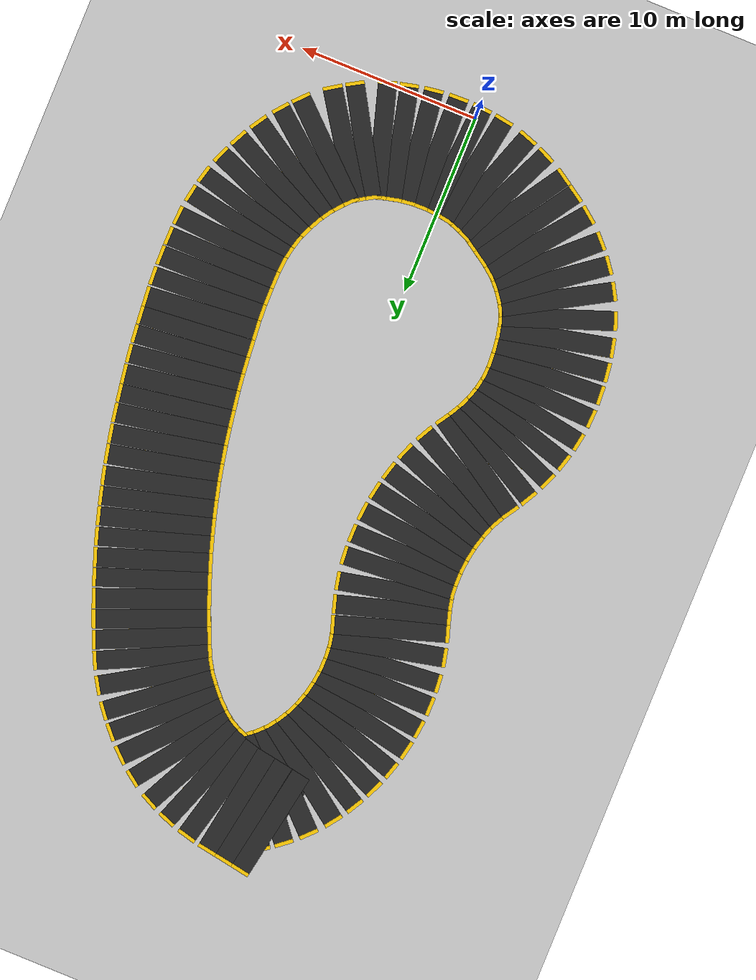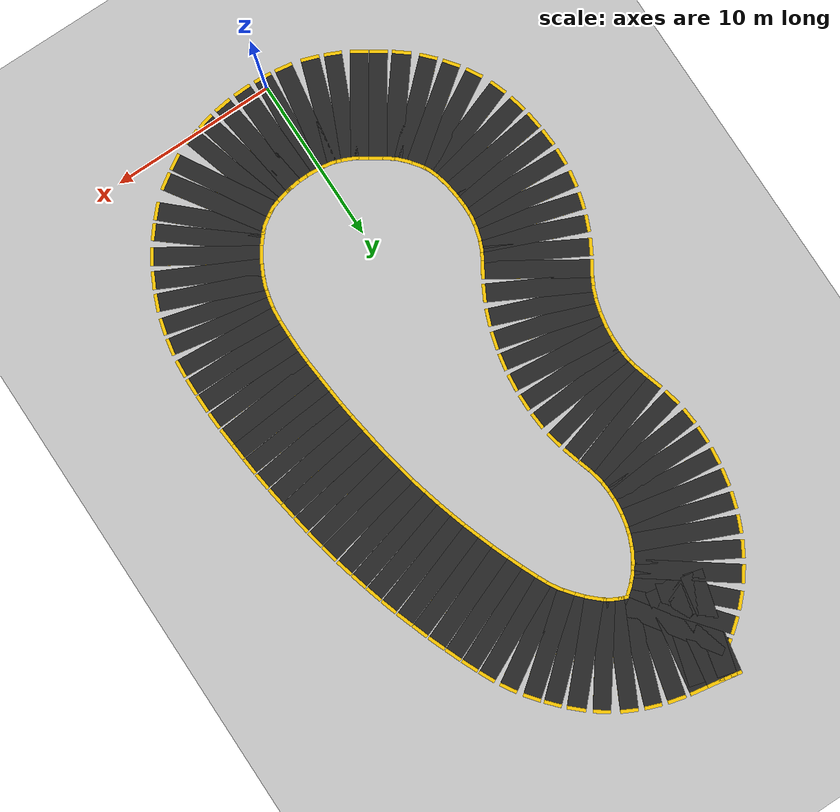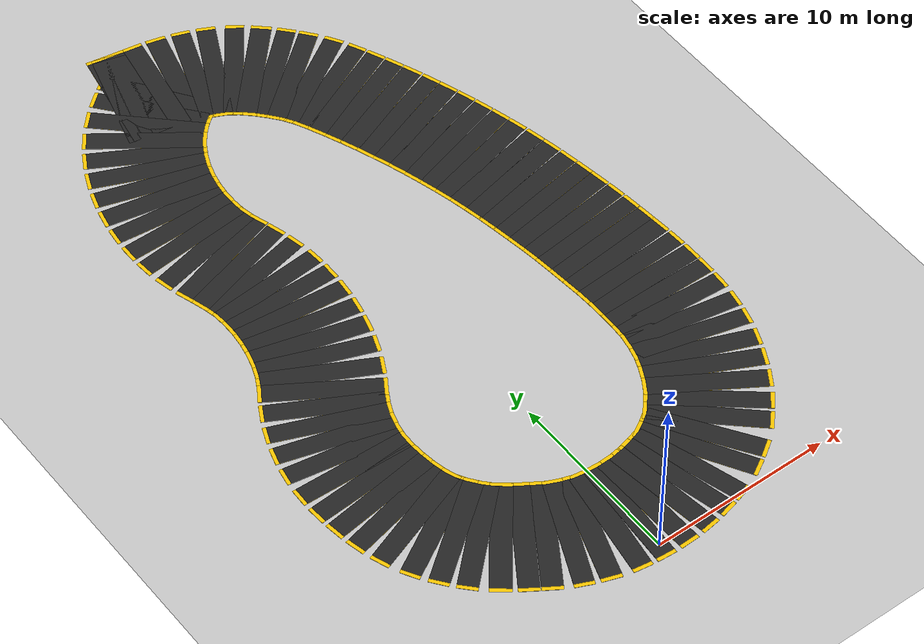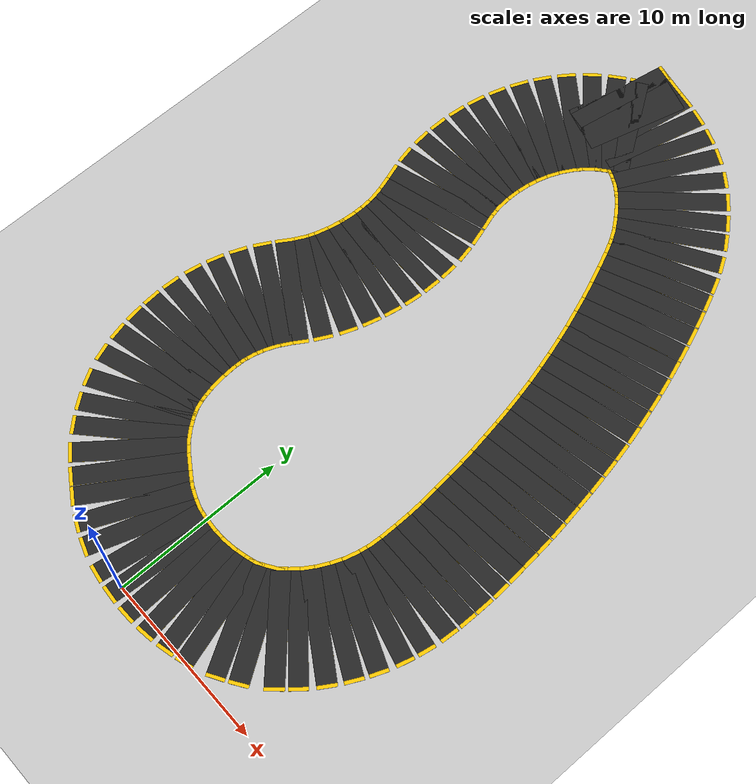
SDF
<sdf version="1.7">
 <world name="custom_road_world">
  <scene><ambient>1.0 1.0 1.0</ambient><background>0.8 0.8 0.8</background></scene>
  <plugin filename="ignition-gazebo-physics-system" name="ignition::gazebo::systems::Physics"/>
  <plugin filename="ignition-gazebo-sensors-system" name="ignition::gazebo::systems::Sensors">
   <render_engine>ogre2</render_engine>
  </plugin>
  <plugin filename="ignition-gazebo-user-commands-system" name="ignition::gazebo::systems::UserCommands"/>
  <plugin filename="ignition-gazebo-scene-broadcaster-system" name="ignition::gazebo::systems::SceneBroadcaster"/>
  <model name="ground_plane">
   <static>true</static>
   <link name="link">
    <collision name="collision">
     <geometry><plane><normal>0 0 1</normal><size>1000 1000</size></plane></geometry>
    </collision>
    <visual name="visual">
     <geometry><plane><normal>0 0 1</normal><size>1000 1000</size></plane></geometry>
     <material>
      <ambient>0.8 0.8 0.8 1</ambient>
      <diffuse>0.8 0.8 0.8 1</diffuse>
      <specular>0.8 0.8 0.8 1</specular>
     </material>
    </visual>
   </link>
  </model>
  <include><uri>https://fuel.ignitionrobotics.org/1.0/openrobotics/models/Sun</uri></include>
  <model name="elliptical_road">
   <static>true</static>
   <link name="seg_0">
    <pose>-4.136 39.092 0.01 0 0 -0.179</pose>
    <visual name="yellow_base_0">
     <pose>0 0 0.001 0 0 0</pose>
     <geometry><box><size>1.060 6.4 0.02</size></box></geometry>
     <material>
      <ambient>1.0 0.8 0.0 1.0</ambient>
      <diffuse>1.0 0.8 0.0 1.0</diffuse>
      <specular>0.1 0.1 0.1 1.0</specular>
     </material>
    </visual>
    <visual name="asphalt_top_0">
     <pose>0 0 0.002 0 0 0</pose>
     <geometry><box><size>1.060 6.0 0.02</size></box></geometry>
     <material>
      <ambient>0.15 0.15 0.15 1.0</ambient>
      <diffuse>0.15 0.15 0.15 1.0</diffuse>
      <specular>0.05 0.05 0.05 1.0</specular>
     </material>
    </visual>
    <visual name="center_line_0">
     <pose>0 0 0.003 0 0 0</pose>
     <geometry><box><size>0.530 0.15 0.001</size></box></geometry>
     <material><ambient>0.9 0.9 0.9 1</ambient><diffuse>0.9 0.9 0.9 1</diffuse></material>
    </visual>
   </link>
   <link name="seg_1">
    <pose>-3.084 38.909 0.01 0 0 -0.166</pose>
    <visual name="yellow_base_1">
     <pose>0 0 0.001 0 0 0</pose>
     <geometry><box><size>1.077 6.4 0.02</size></box></geometry>
     <material>
      <ambient>1.0 0.8 0.0 1.0</ambient>
      <diffuse>1.0 0.8 0.0 1.0</diffuse>
      <specular>0.1 0.1 0.1 1.0</specular>
     </material>
    </visual>
    <visual name="asphalt_top_1">
     <pose>0 0 0.002 0 0 0</pose>
     <geometry><box><size>1.077 6.0 0.02</size></box></geometry>
     <material>
      <ambient>0.15 0.15 0.15 1.0</ambient>
      <diffuse>0.15 0.15 0.15 1.0</diffuse>
      <specular>0.05 0.05 0.05 1.0</specular>
     </material>
    </visual>
    <visual name="center_line_1">
     <pose>0 0 0.003 0 0 0</pose>
     <geometry><box><size>0.538 0.15 0.001</size></box></geometry>
     <material><ambient>0.9 0.9 0.9 1</ambient><diffuse>0.9 0.9 0.9 1</diffuse></material>
    </visual>
   </link>
   <link name="seg_2">
    <pose>-2.030 38.733 0.01 0 0 -0.165</pose>
    <visual name="yellow_base_2">
     <pose>0 0 0.001 0 0 0</pose>
     <geometry><box><size>1.059 6.4 0.02</size></box></geometry>
     <material>
      <ambient>1.0 0.8 0.0 1.0</ambient>
      <diffuse>1.0 0.8 0.0 1.0</diffuse>
      <specular>0.1 0.1 0.1 1.0</specular>
     </material>
    </visual>
    <visual name="asphalt_top_2">
     <pose>0 0 0.002 0 0 0</pose>
     <geometry><box><size>1.059 6.0 0.02</size></box></geometry>
     <material>
      <ambient>0.15 0.15 0.15 1.0</ambient>
      <diffuse>0.15 0.15 0.15 1.0</diffuse>
      <specular>0.05 0.05 0.05 1.0</specular>
     </material>
    </visual>
    <visual name="center_line_2">
     <pose>0 0 0.003 0 0 0</pose>
     <geometry><box><size>0.529 0.15 0.001</size></box></geometry>
     <material><ambient>0.9 0.9 0.9 1</ambient><diffuse>0.9 0.9 0.9 1</diffuse></material>
    </visual>
   </link>
   <link name="seg_3">
    <pose>-0.987 38.514 0.01 0 0 -0.247</pose>
    <visual name="yellow_base_3">
     <pose>0 0 0.001 0 0 0</pose>
     <geometry><box><size>1.075 6.4 0.02</size></box></geometry>
     <material>
      <ambient>1.0 0.8 0.0 1.0</ambient>
      <diffuse>1.0 0.8 0.0 1.0</diffuse>
      <specular>0.1 0.1 0.1 1.0</specular>
     </material>
    </visual>
    <visual name="asphalt_top_3">
     <pose>0 0 0.002 0 0 0</pose>
     <geometry><box><size>1.075 6.0 0.02</size></box></geometry>
     <material>
      <ambient>0.15 0.15 0.15 1.0</ambient>
      <diffuse>0.15 0.15 0.15 1.0</diffuse>
      <specular>0.05 0.05 0.05 1.0</specular>
     </material>
    </visual>
    <visual name="center_line_3">
     <pose>0 0 0.003 0 0 0</pose>
     <geometry><box><size>0.537 0.15 0.001</size></box></geometry>
     <material><ambient>0.9 0.9 0.9 1</ambient><diffuse>0.9 0.9 0.9 1</diffuse></material>
    </visual>
   </link>
   <link name="seg_4">
    <pose>0.007 38.207 0.01 0 0 -0.355</pose>
    <visual name="yellow_base_4">
     <pose>0 0 0.001 0 0 0</pose>
     <geometry><box><size>1.010 6.4 0.02</size></box></geometry>
     <material>
      <ambient>1.0 0.8 0.0 1.0</ambient>
      <diffuse>1.0 0.8 0.0 1.0</diffuse>
      <specular>0.1 0.1 0.1 1.0</specular>
     </material>
    </visual>
    <visual name="asphalt_top_4">
     <pose>0 0 0.002 0 0 0</pose>
     <geometry><box><size>1.010 6.0 0.02</size></box></geometry>
     <material>
      <ambient>0.15 0.15 0.15 1.0</ambient>
      <diffuse>0.15 0.15 0.15 1.0</diffuse>
      <specular>0.05 0.05 0.05 1.0</specular>
     </material>
    </visual>
    <visual name="center_line_4">
     <pose>0 0 0.003 0 0 0</pose>
     <geometry><box><size>0.505 0.15 0.001</size></box></geometry>
     <material><ambient>0.9 0.9 0.9 1</ambient><diffuse>0.9 0.9 0.9 1</diffuse></material>
    </visual>
   </link>
   <link name="seg_5">
    <pose>0.940 37.802 0.01 0 0 -0.464</pose>
    <visual name="yellow_base_5">
     <pose>0 0 0.001 0 0 0</pose>
     <geometry><box><size>1.027 6.4 0.02</size></box></geometry>
     <material>
      <ambient>1.0 0.8 0.0 1.0</ambient>
      <diffuse>1.0 0.8 0.0 1.0</diffuse>
      <specular>0.1 0.1 0.1 1.0</specular>
     </material>
    </visual>
    <visual name="asphalt_top_5">
     <pose>0 0 0.002 0 0 0</pose>
     <geometry><box><size>1.027 6.0 0.02</size></box></geometry>
     <material>
      <ambient>0.15 0.15 0.15 1.0</ambient>
      <diffuse>0.15 0.15 0.15 1.0</diffuse>
      <specular>0.05 0.05 0.05 1.0</specular>
     </material>
    </visual>
    <visual name="center_line_5">
     <pose>0 0 0.003 0 0 0</pose>
     <geometry><box><size>0.514 0.15 0.001</size></box></geometry>
     <material><ambient>0.9 0.9 0.9 1</ambient><diffuse>0.9 0.9 0.9 1</diffuse></material>
    </visual>
   </link>
   <link name="seg_6">
    <pose>1.809 37.273 0.01 0 0 -0.630</pose>
    <visual name="yellow_base_6">
     <pose>0 0 0.001 0 0 0</pose>
     <geometry><box><size>1.013 6.4 0.02</size></box></geometry>
     <material>
      <ambient>1.0 0.8 0.0 1.0</ambient>
      <diffuse>1.0 0.8 0.0 1.0</diffuse>
      <specular>0.1 0.1 0.1 1.0</specular>
     </material>
    </visual>
    <visual name="asphalt_top_6">
     <pose>0 0 0.002 0 0 0</pose>
     <geometry><box><size>1.013 6.0 0.02</size></box></geometry>
     <material>
      <ambient>0.15 0.15 0.15 1.0</ambient>
      <diffuse>0.15 0.15 0.15 1.0</diffuse>
      <specular>0.05 0.05 0.05 1.0</specular>
     </material>
    </visual>
    <visual name="center_line_6">
     <pose>0 0 0.003 0 0 0</pose>
     <geometry><box><size>0.507 0.15 0.001</size></box></geometry>
     <material><ambient>0.9 0.9 0.9 1</ambient><diffuse>0.9 0.9 0.9 1</diffuse></material>
    </visual>
   </link>
   <link name="seg_7">
    <pose>2.620 36.603 0.01 0 0 -0.748</pose>
    <visual name="yellow_base_7">
     <pose>0 0 0.001 0 0 0</pose>
     <geometry><box><size>1.094 6.4 0.02</size></box></geometry>
     <material>
      <ambient>1.0 0.8 0.0 1.0</ambient>
      <diffuse>1.0 0.8 0.0 1.0</diffuse>
      <specular>0.1 0.1 0.1 1.0</specular>
     </material>
    </visual>
    <visual name="asphalt_top_7">
     <pose>0 0 0.002 0 0 0</pose>
     <geometry><box><size>1.094 6.0 0.02</size></box></geometry>
     <material>
      <ambient>0.15 0.15 0.15 1.0</ambient>
      <diffuse>0.15 0.15 0.15 1.0</diffuse>
      <specular>0.05 0.05 0.05 1.0</specular>
     </material>
    </visual>
    <visual name="center_line_7">
     <pose>0 0 0.003 0 0 0</pose>
     <geometry><box><size>0.547 0.15 0.001</size></box></geometry>
     <material><ambient>0.9 0.9 0.9 1</ambient><diffuse>0.9 0.9 0.9 1</diffuse></material>
    </visual>
   </link>
   <link name="seg_8">
    <pose>3.358 35.854 0.01 0 0 -0.841</pose>
    <visual name="yellow_base_8">
     <pose>0 0 0.001 0 0 0</pose>
     <geometry><box><size>1.011 6.4 0.02</size></box></geometry>
     <material>
      <ambient>1.0 0.8 0.0 1.0</ambient>
      <diffuse>1.0 0.8 0.0 1.0</diffuse>
      <specular>0.1 0.1 0.1 1.0</specular>
     </material>
    </visual>
    <visual name="asphalt_top_8">
     <pose>0 0 0.002 0 0 0</pose>
     <geometry><box><size>1.011 6.0 0.02</size></box></geometry>
     <material>
      <ambient>0.15 0.15 0.15 1.0</ambient>
      <diffuse>0.15 0.15 0.15 1.0</diffuse>
      <specular>0.05 0.05 0.05 1.0</specular>
     </material>
    </visual>
    <visual name="center_line_8">
     <pose>0 0 0.003 0 0 0</pose>
     <geometry><box><size>0.506 0.15 0.001</size></box></geometry>
     <material><ambient>0.9 0.9 0.9 1</ambient><diffuse>0.9 0.9 0.9 1</diffuse></material>
    </visual>
   </link>
   <link name="seg_9">
    <pose>4.017 35.072 0.01 0 0 -0.900</pose>
    <visual name="yellow_base_9">
     <pose>0 0 0.001 0 0 0</pose>
     <geometry><box><size>1.035 6.4 0.02</size></box></geometry>
     <material>
      <ambient>1.0 0.8 0.0 1.0</ambient>
      <diffuse>1.0 0.8 0.0 1.0</diffuse>
      <specular>0.1 0.1 0.1 1.0</specular>
     </material>
    </visual>
    <visual name="asphalt_top_9">
     <pose>0 0 0.002 0 0 0</pose>
     <geometry><box><size>1.035 6.0 0.02</size></box></geometry>
     <material>
      <ambient>0.15 0.15 0.15 1.0</ambient>
      <diffuse>0.15 0.15 0.15 1.0</diffuse>
      <specular>0.05 0.05 0.05 1.0</specular>
     </material>
    </visual>
    <visual name="center_line_9">
     <pose>0 0 0.003 0 0 0</pose>
     <geometry><box><size>0.517 0.15 0.001</size></box></geometry>
     <material><ambient>0.9 0.9 0.9 1</ambient><diffuse>0.9 0.9 0.9 1</diffuse></material>
    </visual>
   </link>
   <link name="seg_10">
    <pose>4.613 34.221 0.01 0 0 -1.019</pose>
    <visual name="yellow_base_10">
     <pose>0 0 0.001 0 0 0</pose>
     <geometry><box><size>1.047 6.4 0.02</size></box></geometry>
     <material>
      <ambient>1.0 0.8 0.0 1.0</ambient>
      <diffuse>1.0 0.8 0.0 1.0</diffuse>
      <specular>0.1 0.1 0.1 1.0</specular>
     </material>
    </visual>
    <visual name="asphalt_top_10">
     <pose>0 0 0.002 0 0 0</pose>
     <geometry><box><size>1.047 6.0 0.02</size></box></geometry>
     <material>
      <ambient>0.15 0.15 0.15 1.0</ambient>
      <diffuse>0.15 0.15 0.15 1.0</diffuse>
      <specular>0.05 0.05 0.05 1.0</specular>
     </material>
    </visual>
    <visual name="center_line_10">
     <pose>0 0 0.003 0 0 0</pose>
     <geometry><box><size>0.523 0.15 0.001</size></box></geometry>
     <material><ambient>0.9 0.9 0.9 1</ambient><diffuse>0.9 0.9 0.9 1</diffuse></material>
    </visual>
   </link>
   <link name="seg_11">
    <pose>5.107 33.319 0.01 0 0 -1.123</pose>
    <visual name="yellow_base_11">
     <pose>0 0 0.001 0 0 0</pose>
     <geometry><box><size>1.015 6.4 0.02</size></box></geometry>
     <material>
      <ambient>1.0 0.8 0.0 1.0</ambient>
      <diffuse>1.0 0.8 0.0 1.0</diffuse>
      <specular>0.1 0.1 0.1 1.0</specular>
     </material>
    </visual>
    <visual name="asphalt_top_11">
     <pose>0 0 0.002 0 0 0</pose>
     <geometry><box><size>1.015 6.0 0.02</size></box></geometry>
     <material>
      <ambient>0.15 0.15 0.15 1.0</ambient>
      <diffuse>0.15 0.15 0.15 1.0</diffuse>
      <specular>0.05 0.05 0.05 1.0</specular>
     </material>
    </visual>
    <visual name="center_line_11">
     <pose>0 0 0.003 0 0 0</pose>
     <geometry><box><size>0.507 0.15 0.001</size></box></geometry>
     <material><ambient>0.9 0.9 0.9 1</ambient><diffuse>0.9 0.9 0.9 1</diffuse></material>
    </visual>
   </link>
   <link name="seg_12">
    <pose>5.535 32.388 0.01 0 0 -1.155</pose>
    <visual name="yellow_base_12">
     <pose>0 0 0.001 0 0 0</pose>
     <geometry><box><size>1.035 6.4 0.02</size></box></geometry>
     <material>
      <ambient>1.0 0.8 0.0 1.0</ambient>
      <diffuse>1.0 0.8 0.0 1.0</diffuse>
      <specular>0.1 0.1 0.1 1.0</specular>
     </material>
    </visual>
    <visual name="asphalt_top_12">
     <pose>0 0 0.002 0 0 0</pose>
     <geometry><box><size>1.035 6.0 0.02</size></box></geometry>
     <material>
      <ambient>0.15 0.15 0.15 1.0</ambient>
      <diffuse>0.15 0.15 0.15 1.0</diffuse>
      <specular>0.05 0.05 0.05 1.0</specular>
     </material>
    </visual>
    <visual name="center_line_12">
     <pose>0 0 0.003 0 0 0</pose>
     <geometry><box><size>0.518 0.15 0.001</size></box></geometry>
     <material><ambient>0.9 0.9 0.9 1</ambient><diffuse>0.9 0.9 0.9 1</diffuse></material>
    </visual>
   </link>
   <link name="seg_13">
    <pose>5.941 31.437 0.01 0 0 -1.179</pose>
    <visual name="yellow_base_13">
     <pose>0 0 0.001 0 0 0</pose>
     <geometry><box><size>1.031 6.4 0.02</size></box></geometry>
     <material>
      <ambient>1.0 0.8 0.0 1.0</ambient>
      <diffuse>1.0 0.8 0.0 1.0</diffuse>
      <specular>0.1 0.1 0.1 1.0</specular>
     </material>
    </visual>
    <visual name="asphalt_top_13">
     <pose>0 0 0.002 0 0 0</pose>
     <geometry><box><size>1.031 6.0 0.02</size></box></geometry>
     <material>
      <ambient>0.15 0.15 0.15 1.0</ambient>
      <diffuse>0.15 0.15 0.15 1.0</diffuse>
      <specular>0.05 0.05 0.05 1.0</specular>
     </material>
    </visual>
    <visual name="center_line_13">
     <pose>0 0 0.003 0 0 0</pose>
     <geometry><box><size>0.516 0.15 0.001</size></box></geometry>
     <material><ambient>0.9 0.9 0.9 1</ambient><diffuse>0.9 0.9 0.9 1</diffuse></material>
    </visual>
   </link>
   <link name="seg_14">
    <pose>6.339 30.451 0.01 0 0 -1.196</pose>
    <visual name="yellow_base_14">
     <pose>0 0 0.001 0 0 0</pose>
     <geometry><box><size>1.096 6.4 0.02</size></box></geometry>
     <material>
      <ambient>1.0 0.8 0.0 1.0</ambient>
      <diffuse>1.0 0.8 0.0 1.0</diffuse>
      <specular>0.1 0.1 0.1 1.0</specular>
     </material>
    </visual>
    <visual name="asphalt_top_14">
     <pose>0 0 0.002 0 0 0</pose>
     <geometry><box><size>1.096 6.0 0.02</size></box></geometry>
     <material>
      <ambient>0.15 0.15 0.15 1.0</ambient>
      <diffuse>0.15 0.15 0.15 1.0</diffuse>
      <specular>0.05 0.05 0.05 1.0</specular>
     </material>
    </visual>
    <visual name="center_line_14">
     <pose>0 0 0.003 0 0 0</pose>
     <geometry><box><size>0.548 0.15 0.001</size></box></geometry>
     <material><ambient>0.9 0.9 0.9 1</ambient><diffuse>0.9 0.9 0.9 1</diffuse></material>
    </visual>
   </link>
   <link name="seg_15">
    <pose>6.711 29.463 0.01 0 0 -1.226</pose>
    <visual name="yellow_base_15">
     <pose>0 0 0.001 0 0 0</pose>
     <geometry><box><size>1.014 6.4 0.02</size></box></geometry>
     <material>
      <ambient>1.0 0.8 0.0 1.0</ambient>
      <diffuse>1.0 0.8 0.0 1.0</diffuse>
      <specular>0.1 0.1 0.1 1.0</specular>
     </material>
    </visual>
    <visual name="asphalt_top_15">
     <pose>0 0 0.002 0 0 0</pose>
     <geometry><box><size>1.014 6.0 0.02</size></box></geometry>
     <material>
      <ambient>0.15 0.15 0.15 1.0</ambient>
      <diffuse>0.15 0.15 0.15 1.0</diffuse>
      <specular>0.05 0.05 0.05 1.0</specular>
     </material>
    </visual>
    <visual name="center_line_15">
     <pose>0 0 0.003 0 0 0</pose>
     <geometry><box><size>0.507 0.15 0.001</size></box></geometry>
     <material><ambient>0.9 0.9 0.9 1</ambient><diffuse>0.9 0.9 0.9 1</diffuse></material>
    </visual>
   </link>
   <link name="seg_16">
    <pose>7.058 28.483 0.01 0 0 -1.235</pose>
    <visual name="yellow_base_16">
     <pose>0 0 0.001 0 0 0</pose>
     <geometry><box><size>1.065 6.4 0.02</size></box></geometry>
     <material>
      <ambient>1.0 0.8 0.0 1.0</ambient>
      <diffuse>1.0 0.8 0.0 1.0</diffuse>
      <specular>0.1 0.1 0.1 1.0</specular>
     </material>
    </visual>
    <visual name="asphalt_top_16">
     <pose>0 0 0.002 0 0 0</pose>
     <geometry><box><size>1.065 6.0 0.02</size></box></geometry>
     <material>
      <ambient>0.15 0.15 0.15 1.0</ambient>
      <diffuse>0.15 0.15 0.15 1.0</diffuse>
      <specular>0.05 0.05 0.05 1.0</specular>
     </material>
    </visual>
    <visual name="center_line_16">
     <pose>0 0 0.003 0 0 0</pose>
     <geometry><box><size>0.533 0.15 0.001</size></box></geometry>
     <material><ambient>0.9 0.9 0.9 1</ambient><diffuse>0.9 0.9 0.9 1</diffuse></material>
    </visual>
   </link>
   <link name="seg_17">
    <pose>7.387 27.496 0.01 0 0 -1.263</pose>
    <visual name="yellow_base_17">
     <pose>0 0 0.001 0 0 0</pose>
     <geometry><box><size>1.016 6.4 0.02</size></box></geometry>
     <material>
      <ambient>1.0 0.8 0.0 1.0</ambient>
      <diffuse>1.0 0.8 0.0 1.0</diffuse>
      <specular>0.1 0.1 0.1 1.0</specular>
     </material>
    </visual>
    <visual name="asphalt_top_17">
     <pose>0 0 0.002 0 0 0</pose>
     <geometry><box><size>1.016 6.0 0.02</size></box></geometry>
     <material>
      <ambient>0.15 0.15 0.15 1.0</ambient>
      <diffuse>0.15 0.15 0.15 1.0</diffuse>
      <specular>0.05 0.05 0.05 1.0</specular>
     </material>
    </visual>
    <visual name="center_line_17">
     <pose>0 0 0.003 0 0 0</pose>
     <geometry><box><size>0.508 0.15 0.001</size></box></geometry>
     <material><ambient>0.9 0.9 0.9 1</ambient><diffuse>0.9 0.9 0.9 1</diffuse></material>
    </visual>
   </link>
   <link name="seg_18">
    <pose>7.687 26.514 0.01 0 0 -1.286</pose>
    <visual name="yellow_base_18">
     <pose>0 0 0.001 0 0 0</pose>
     <geometry><box><size>1.036 6.4 0.02</size></box></geometry>
     <material>
      <ambient>1.0 0.8 0.0 1.0</ambient>
      <diffuse>1.0 0.8 0.0 1.0</diffuse>
      <specular>0.1 0.1 0.1 1.0</specular>
     </material>
    </visual>
    <visual name="asphalt_top_18">
     <pose>0 0 0.002 0 0 0</pose>
     <geometry><box><size>1.036 6.0 0.02</size></box></geometry>
     <material>
      <ambient>0.15 0.15 0.15 1.0</ambient>
      <diffuse>0.15 0.15 0.15 1.0</diffuse>
      <specular>0.05 0.05 0.05 1.0</specular>
     </material>
    </visual>
    <visual name="center_line_18">
     <pose>0 0 0.003 0 0 0</pose>
     <geometry><box><size>0.518 0.15 0.001</size></box></geometry>
     <material><ambient>0.9 0.9 0.9 1</ambient><diffuse>0.9 0.9 0.9 1</diffuse></material>
    </visual>
   </link>
   <link name="seg_19">
    <pose>7.968 25.517 0.01 0 0 -1.306</pose>
    <visual name="yellow_base_19">
     <pose>0 0 0.001 0 0 0</pose>
     <geometry><box><size>1.037 6.4 0.02</size></box></geometry>
     <material>
      <ambient>1.0 0.8 0.0 1.0</ambient>
      <diffuse>1.0 0.8 0.0 1.0</diffuse>
      <specular>0.1 0.1 0.1 1.0</specular>
     </material>
    </visual>
    <visual name="asphalt_top_19">
     <pose>0 0 0.002 0 0 0</pose>
     <geometry><box><size>1.037 6.0 0.02</size></box></geometry>
     <material>
      <ambient>0.15 0.15 0.15 1.0</ambient>
      <diffuse>0.15 0.15 0.15 1.0</diffuse>
      <specular>0.05 0.05 0.05 1.0</specular>
     </material>
    </visual>
    <visual name="center_line_19">
     <pose>0 0 0.003 0 0 0</pose>
     <geometry><box><size>0.519 0.15 0.001</size></box></geometry>
     <material><ambient>0.9 0.9 0.9 1</ambient><diffuse>0.9 0.9 0.9 1</diffuse></material>
    </visual>
   </link>
   <link name="seg_20">
    <pose>8.234 24.505 0.01 0 0 -1.322</pose>
    <visual name="yellow_base_20">
     <pose>0 0 0.001 0 0 0</pose>
     <geometry><box><size>1.055 6.4 0.02</size></box></geometry>
     <material>
      <ambient>1.0 0.8 0.0 1.0</ambient>
      <diffuse>1.0 0.8 0.0 1.0</diffuse>
      <specular>0.1 0.1 0.1 1.0</specular>
     </material>
    </visual>
    <visual name="asphalt_top_20">
     <pose>0 0 0.002 0 0 0</pose>
     <geometry><box><size>1.055 6.0 0.02</size></box></geometry>
     <material>
      <ambient>0.15 0.15 0.15 1.0</ambient>
      <diffuse>0.15 0.15 0.15 1.0</diffuse>
      <specular>0.05 0.05 0.05 1.0</specular>
     </material>
    </visual>
    <visual name="center_line_20">
     <pose>0 0 0.003 0 0 0</pose>
     <geometry><box><size>0.527 0.15 0.001</size></box></geometry>
     <material><ambient>0.9 0.9 0.9 1</ambient><diffuse>0.9 0.9 0.9 1</diffuse></material>
    </visual>
   </link>
   <link name="seg_21">
    <pose>8.477 23.471 0.01 0 0 -1.358</pose>
    <visual name="yellow_base_21">
     <pose>0 0 0.001 0 0 0</pose>
     <geometry><box><size>1.070 6.4 0.02</size></box></geometry>
     <material>
      <ambient>1.0 0.8 0.0 1.0</ambient>
      <diffuse>1.0 0.8 0.0 1.0</diffuse>
      <specular>0.1 0.1 0.1 1.0</specular>
     </material>
    </visual>
    <visual name="asphalt_top_21">
     <pose>0 0 0.002 0 0 0</pose>
     <geometry><box><size>1.070 6.0 0.02</size></box></geometry>
     <material>
      <ambient>0.15 0.15 0.15 1.0</ambient>
      <diffuse>0.15 0.15 0.15 1.0</diffuse>
      <specular>0.05 0.05 0.05 1.0</specular>
     </material>
    </visual>
    <visual name="center_line_21">
     <pose>0 0 0.003 0 0 0</pose>
     <geometry><box><size>0.535 0.15 0.001</size></box></geometry>
     <material><ambient>0.9 0.9 0.9 1</ambient><diffuse>0.9 0.9 0.9 1</diffuse></material>
    </visual>
   </link>
   <link name="seg_22">
    <pose>8.695 22.428 0.01 0 0 -1.372</pose>
    <visual name="yellow_base_22">
     <pose>0 0 0.001 0 0 0</pose>
     <geometry><box><size>1.062 6.4 0.02</size></box></geometry>
     <material>
      <ambient>1.0 0.8 0.0 1.0</ambient>
      <diffuse>1.0 0.8 0.0 1.0</diffuse>
      <specular>0.1 0.1 0.1 1.0</specular>
     </material>
    </visual>
    <visual name="asphalt_top_22">
     <pose>0 0 0.002 0 0 0</pose>
     <geometry><box><size>1.062 6.0 0.02</size></box></geometry>
     <material>
      <ambient>0.15 0.15 0.15 1.0</ambient>
      <diffuse>0.15 0.15 0.15 1.0</diffuse>
      <specular>0.05 0.05 0.05 1.0</specular>
     </material>
    </visual>
    <visual name="center_line_22">
     <pose>0 0 0.003 0 0 0</pose>
     <geometry><box><size>0.531 0.15 0.001</size></box></geometry>
     <material><ambient>0.9 0.9 0.9 1</ambient><diffuse>0.9 0.9 0.9 1</diffuse></material>
    </visual>
   </link>
   <link name="seg_23">
    <pose>8.891 21.382 0.01 0 0 -1.399</pose>
    <visual name="yellow_base_23">
     <pose>0 0 0.001 0 0 0</pose>
     <geometry><box><size>1.065 6.4 0.02</size></box></geometry>
     <material>
      <ambient>1.0 0.8 0.0 1.0</ambient>
      <diffuse>1.0 0.8 0.0 1.0</diffuse>
      <specular>0.1 0.1 0.1 1.0</specular>
     </material>
    </visual>
    <visual name="asphalt_top_23">
     <pose>0 0 0.002 0 0 0</pose>
     <geometry><box><size>1.065 6.0 0.02</size></box></geometry>
     <material>
      <ambient>0.15 0.15 0.15 1.0</ambient>
      <diffuse>0.15 0.15 0.15 1.0</diffuse>
      <specular>0.05 0.05 0.05 1.0</specular>
     </material>
    </visual>
    <visual name="center_line_23">
     <pose>0 0 0.003 0 0 0</pose>
     <geometry><box><size>0.532 0.15 0.001</size></box></geometry>
     <material><ambient>0.9 0.9 0.9 1</ambient><diffuse>0.9 0.9 0.9 1</diffuse></material>
    </visual>
   </link>
   <link name="seg_24">
    <pose>9.060 20.363 0.01 0 0 -1.415</pose>
    <visual name="yellow_base_24">
     <pose>0 0 0.001 0 0 0</pose>
     <geometry><box><size>1.002 6.4 0.02</size></box></geometry>
     <material>
      <ambient>1.0 0.8 0.0 1.0</ambient>
      <diffuse>1.0 0.8 0.0 1.0</diffuse>
      <specular>0.1 0.1 0.1 1.0</specular>
     </material>
    </visual>
    <visual name="asphalt_top_24">
     <pose>0 0 0.002 0 0 0</pose>
     <geometry><box><size>1.002 6.0 0.02</size></box></geometry>
     <material>
      <ambient>0.15 0.15 0.15 1.0</ambient>
      <diffuse>0.15 0.15 0.15 1.0</diffuse>
      <specular>0.05 0.05 0.05 1.0</specular>
     </material>
    </visual>
    <visual name="center_line_24">
     <pose>0 0 0.003 0 0 0</pose>
     <geometry><box><size>0.501 0.15 0.001</size></box></geometry>
     <material><ambient>0.9 0.9 0.9 1</ambient><diffuse>0.9 0.9 0.9 1</diffuse></material>
    </visual>
   </link>
   <link name="seg_25">
    <pose>9.219 19.332 0.01 0 0 -1.419</pose>
    <visual name="yellow_base_25">
     <pose>0 0 0.001 0 0 0</pose>
     <geometry><box><size>1.084 6.4 0.02</size></box></geometry>
     <material>
      <ambient>1.0 0.8 0.0 1.0</ambient>
      <diffuse>1.0 0.8 0.0 1.0</diffuse>
      <specular>0.1 0.1 0.1 1.0</specular>
     </material>
    </visual>
    <visual name="asphalt_top_25">
     <pose>0 0 0.002 0 0 0</pose>
     <geometry><box><size>1.084 6.0 0.02</size></box></geometry>
     <material>
      <ambient>0.15 0.15 0.15 1.0</ambient>
      <diffuse>0.15 0.15 0.15 1.0</diffuse>
      <specular>0.05 0.05 0.05 1.0</specular>
     </material>
    </visual>
    <visual name="center_line_25">
     <pose>0 0 0.003 0 0 0</pose>
     <geometry><box><size>0.542 0.15 0.001</size></box></geometry>
     <material><ambient>0.9 0.9 0.9 1</ambient><diffuse>0.9 0.9 0.9 1</diffuse></material>
    </visual>
   </link>
   <link name="seg_26">
    <pose>9.366 18.288 0.01 0 0 -1.445</pose>
    <visual name="yellow_base_26">
     <pose>0 0 0.001 0 0 0</pose>
     <geometry><box><size>1.025 6.4 0.02</size></box></geometry>
     <material>
      <ambient>1.0 0.8 0.0 1.0</ambient>
      <diffuse>1.0 0.8 0.0 1.0</diffuse>
      <specular>0.1 0.1 0.1 1.0</specular>
     </material>
    </visual>
    <visual name="asphalt_top_26">
     <pose>0 0 0.002 0 0 0</pose>
     <geometry><box><size>1.025 6.0 0.02</size></box></geometry>
     <material>
      <ambient>0.15 0.15 0.15 1.0</ambient>
      <diffuse>0.15 0.15 0.15 1.0</diffuse>
      <specular>0.05 0.05 0.05 1.0</specular>
     </material>
    </visual>
    <visual name="center_line_26">
     <pose>0 0 0.003 0 0 0</pose>
     <geometry><box><size>0.513 0.15 0.001</size></box></geometry>
     <material><ambient>0.9 0.9 0.9 1</ambient><diffuse>0.9 0.9 0.9 1</diffuse></material>
    </visual>
   </link>
   <link name="seg_27">
    <pose>9.481 17.274 0.01 0 0 -1.472</pose>
    <visual name="yellow_base_27">
     <pose>0 0 0.001 0 0 0</pose>
     <geometry><box><size>1.015 6.4 0.02</size></box></geometry>
     <material>
      <ambient>1.0 0.8 0.0 1.0</ambient>
      <diffuse>1.0 0.8 0.0 1.0</diffuse>
      <specular>0.1 0.1 0.1 1.0</specular>
     </material>
    </visual>
    <visual name="asphalt_top_27">
     <pose>0 0 0.002 0 0 0</pose>
     <geometry><box><size>1.015 6.0 0.02</size></box></geometry>
     <material>
      <ambient>0.15 0.15 0.15 1.0</ambient>
      <diffuse>0.15 0.15 0.15 1.0</diffuse>
      <specular>0.05 0.05 0.05 1.0</specular>
     </material>
    </visual>
    <visual name="center_line_27">
     <pose>0 0 0.003 0 0 0</pose>
     <geometry><box><size>0.508 0.15 0.001</size></box></geometry>
     <material><ambient>0.9 0.9 0.9 1</ambient><diffuse>0.9 0.9 0.9 1</diffuse></material>
    </visual>
   </link>
   <link name="seg_28">
    <pose>9.575 16.270 0.01 0 0 -1.483</pose>
    <visual name="yellow_base_28">
     <pose>0 0 0.001 0 0 0</pose>
     <geometry><box><size>1.001 6.4 0.02</size></box></geometry>
     <material>
      <ambient>1.0 0.8 0.0 1.0</ambient>
      <diffuse>1.0 0.8 0.0 1.0</diffuse>
      <specular>0.1 0.1 0.1 1.0</specular>
     </material>
    </visual>
    <visual name="asphalt_top_28">
     <pose>0 0 0.002 0 0 0</pose>
     <geometry><box><size>1.001 6.0 0.02</size></box></geometry>
     <material>
      <ambient>0.15 0.15 0.15 1.0</ambient>
      <diffuse>0.15 0.15 0.15 1.0</diffuse>
      <specular>0.05 0.05 0.05 1.0</specular>
     </material>
    </visual>
    <visual name="center_line_28">
     <pose>0 0 0.003 0 0 0</pose>
     <geometry><box><size>0.501 0.15 0.001</size></box></geometry>
     <material><ambient>0.9 0.9 0.9 1</ambient><diffuse>0.9 0.9 0.9 1</diffuse></material>
    </visual>
   </link>
   <link name="seg_29">
    <pose>9.667 15.225 0.01 0 0 -1.482</pose>
    <visual name="yellow_base_29">
     <pose>0 0 0.001 0 0 0</pose>
     <geometry><box><size>1.098 6.4 0.02</size></box></geometry>
     <material>
      <ambient>1.0 0.8 0.0 1.0</ambient>
      <diffuse>1.0 0.8 0.0 1.0</diffuse>
      <specular>0.1 0.1 0.1 1.0</specular>
     </material>
    </visual>
    <visual name="asphalt_top_29">
     <pose>0 0 0.002 0 0 0</pose>
     <geometry><box><size>1.098 6.0 0.02</size></box></geometry>
     <material>
      <ambient>0.15 0.15 0.15 1.0</ambient>
      <diffuse>0.15 0.15 0.15 1.0</diffuse>
      <specular>0.05 0.05 0.05 1.0</specular>
     </material>
    </visual>
    <visual name="center_line_29">
     <pose>0 0 0.003 0 0 0</pose>
     <geometry><box><size>0.549 0.15 0.001</size></box></geometry>
     <material><ambient>0.9 0.9 0.9 1</ambient><diffuse>0.9 0.9 0.9 1</diffuse></material>
    </visual>
   </link>
   <link name="seg_30">
    <pose>9.742 14.170 0.01 0 0 -1.520</pose>
    <visual name="yellow_base_30">
     <pose>0 0 0.001 0 0 0</pose>
     <geometry><box><size>1.018 6.4 0.02</size></box></geometry>
     <material>
      <ambient>1.0 0.8 0.0 1.0</ambient>
      <diffuse>1.0 0.8 0.0 1.0</diffuse>
      <specular>0.1 0.1 0.1 1.0</specular>
     </material>
    </visual>
    <visual name="asphalt_top_30">
     <pose>0 0 0.002 0 0 0</pose>
     <geometry><box><size>1.018 6.0 0.02</size></box></geometry>
     <material>
      <ambient>0.15 0.15 0.15 1.0</ambient>
      <diffuse>0.15 0.15 0.15 1.0</diffuse>
      <specular>0.05 0.05 0.05 1.0</specular>
     </material>
    </visual>
    <visual name="center_line_30">
     <pose>0 0 0.003 0 0 0</pose>
     <geometry><box><size>0.509 0.15 0.001</size></box></geometry>
     <material><ambient>0.9 0.9 0.9 1</ambient><diffuse>0.9 0.9 0.9 1</diffuse></material>
    </visual>
   </link>
   <link name="seg_31">
    <pose>9.773 13.122 0.01 0 0 -1.562</pose>
    <visual name="yellow_base_31">
     <pose>0 0 0.001 0 0 0</pose>
     <geometry><box><size>1.078 6.4 0.02</size></box></geometry>
     <material>
      <ambient>1.0 0.8 0.0 1.0</ambient>
      <diffuse>1.0 0.8 0.0 1.0</diffuse>
      <specular>0.1 0.1 0.1 1.0</specular>
     </material>
    </visual>
    <visual name="asphalt_top_31">
     <pose>0 0 0.002 0 0 0</pose>
     <geometry><box><size>1.078 6.0 0.02</size></box></geometry>
     <material>
      <ambient>0.15 0.15 0.15 1.0</ambient>
      <diffuse>0.15 0.15 0.15 1.0</diffuse>
      <specular>0.05 0.05 0.05 1.0</specular>
     </material>
    </visual>
    <visual name="center_line_31">
     <pose>0 0 0.003 0 0 0</pose>
     <geometry><box><size>0.539 0.15 0.001</size></box></geometry>
     <material><ambient>0.9 0.9 0.9 1</ambient><diffuse>0.9 0.9 0.9 1</diffuse></material>
    </visual>
   </link>
   <link name="seg_32">
    <pose>9.770 12.073 0.01 0 0 -1.585</pose>
    <visual name="yellow_base_32">
     <pose>0 0 0.001 0 0 0</pose>
     <geometry><box><size>1.021 6.4 0.02</size></box></geometry>
     <material>
      <ambient>1.0 0.8 0.0 1.0</ambient>
      <diffuse>1.0 0.8 0.0 1.0</diffuse>
      <specular>0.1 0.1 0.1 1.0</specular>
     </material>
    </visual>
    <visual name="asphalt_top_32">
     <pose>0 0 0.002 0 0 0</pose>
     <geometry><box><size>1.021 6.0 0.02</size></box></geometry>
     <material>
      <ambient>0.15 0.15 0.15 1.0</ambient>
      <diffuse>0.15 0.15 0.15 1.0</diffuse>
      <specular>0.05 0.05 0.05 1.0</specular>
     </material>
    </visual>
    <visual name="center_line_32">
     <pose>0 0 0.003 0 0 0</pose>
     <geometry><box><size>0.510 0.15 0.001</size></box></geometry>
     <material><ambient>0.9 0.9 0.9 1</ambient><diffuse>0.9 0.9 0.9 1</diffuse></material>
    </visual>
   </link>
   <link name="seg_33">
    <pose>9.727 11.039 0.01 0 0 -1.640</pose>
    <visual name="yellow_base_33">
     <pose>0 0 0.001 0 0 0</pose>
     <geometry><box><size>1.050 6.4 0.02</size></box></geometry>
     <material>
      <ambient>1.0 0.8 0.0 1.0</ambient>
      <diffuse>1.0 0.8 0.0 1.0</diffuse>
      <specular>0.1 0.1 0.1 1.0</specular>
     </material>
    </visual>
    <visual name="asphalt_top_33">
     <pose>0 0 0.002 0 0 0</pose>
     <geometry><box><size>1.050 6.0 0.02</size></box></geometry>
     <material>
      <ambient>0.15 0.15 0.15 1.0</ambient>
      <diffuse>0.15 0.15 0.15 1.0</diffuse>
      <specular>0.05 0.05 0.05 1.0</specular>
     </material>
    </visual>
    <visual name="center_line_33">
     <pose>0 0 0.003 0 0 0</pose>
     <geometry><box><size>0.525 0.15 0.001</size></box></geometry>
     <material><ambient>0.9 0.9 0.9 1</ambient><diffuse>0.9 0.9 0.9 1</diffuse></material>
    </visual>
   </link>
   <link name="seg_34">
    <pose>9.599 10.023 0.01 0 0 -1.753</pose>
    <visual name="yellow_base_34">
     <pose>0 0 0.001 0 0 0</pose>
     <geometry><box><size>1.000 6.4 0.02</size></box></geometry>
     <material>
      <ambient>1.0 0.8 0.0 1.0</ambient>
      <diffuse>1.0 0.8 0.0 1.0</diffuse>
      <specular>0.1 0.1 0.1 1.0</specular>
     </material>
    </visual>
    <visual name="asphalt_top_34">
     <pose>0 0 0.002 0 0 0</pose>
     <geometry><box><size>1.000 6.0 0.02</size></box></geometry>
     <material>
      <ambient>0.15 0.15 0.15 1.0</ambient>
      <diffuse>0.15 0.15 0.15 1.0</diffuse>
      <specular>0.05 0.05 0.05 1.0</specular>
     </material>
    </visual>
    <visual name="center_line_34">
     <pose>0 0 0.003 0 0 0</pose>
     <geometry><box><size>0.500 0.15 0.001</size></box></geometry>
     <material><ambient>0.9 0.9 0.9 1</ambient><diffuse>0.9 0.9 0.9 1</diffuse></material>
    </visual>
   </link>
   <link name="seg_35">
    <pose>9.380 9.046 0.01 0 0 -1.829</pose>
    <visual name="yellow_base_35">
     <pose>0 0 0.001 0 0 0</pose>
     <geometry><box><size>1.003 6.4 0.02</size></box></geometry>
     <material>
      <ambient>1.0 0.8 0.0 1.0</ambient>
      <diffuse>1.0 0.8 0.0 1.0</diffuse>
      <specular>0.1 0.1 0.1 1.0</specular>
     </material>
    </visual>
    <visual name="asphalt_top_35">
     <pose>0 0 0.002 0 0 0</pose>
     <geometry><box><size>1.003 6.0 0.02</size></box></geometry>
     <material>
      <ambient>0.15 0.15 0.15 1.0</ambient>
      <diffuse>0.15 0.15 0.15 1.0</diffuse>
      <specular>0.05 0.05 0.05 1.0</specular>
     </material>
    </visual>
    <visual name="center_line_35">
     <pose>0 0 0.003 0 0 0</pose>
     <geometry><box><size>0.502 0.15 0.001</size></box></geometry>
     <material><ambient>0.9 0.9 0.9 1</ambient><diffuse>0.9 0.9 0.9 1</diffuse></material>
    </visual>
   </link>
   <link name="seg_36">
    <pose>9.058 8.078 0.01 0 0 -1.954</pose>
    <visual name="yellow_base_36">
     <pose>0 0 0.001 0 0 0</pose>
     <geometry><box><size>1.041 6.4 0.02</size></box></geometry>
     <material>
      <ambient>1.0 0.8 0.0 1.0</ambient>
      <diffuse>1.0 0.8 0.0 1.0</diffuse>
      <specular>0.1 0.1 0.1 1.0</specular>
     </material>
    </visual>
    <visual name="asphalt_top_36">
     <pose>0 0 0.002 0 0 0</pose>
     <geometry><box><size>1.041 6.0 0.02</size></box></geometry>
     <material>
      <ambient>0.15 0.15 0.15 1.0</ambient>
      <diffuse>0.15 0.15 0.15 1.0</diffuse>
      <specular>0.05 0.05 0.05 1.0</specular>
     </material>
    </visual>
    <visual name="center_line_36">
     <pose>0 0 0.003 0 0 0</pose>
     <geometry><box><size>0.521 0.15 0.001</size></box></geometry>
     <material><ambient>0.9 0.9 0.9 1</ambient><diffuse>0.9 0.9 0.9 1</diffuse></material>
    </visual>
   </link>
   <link name="seg_37">
    <pose>8.627 7.124 0.01 0 0 -2.034</pose>
    <visual name="yellow_base_37">
     <pose>0 0 0.001 0 0 0</pose>
     <geometry><box><size>1.054 6.4 0.02</size></box></geometry>
     <material>
      <ambient>1.0 0.8 0.0 1.0</ambient>
      <diffuse>1.0 0.8 0.0 1.0</diffuse>
      <specular>0.1 0.1 0.1 1.0</specular>
     </material>
    </visual>
    <visual name="asphalt_top_37">
     <pose>0 0 0.002 0 0 0</pose>
     <geometry><box><size>1.054 6.0 0.02</size></box></geometry>
     <material>
      <ambient>0.15 0.15 0.15 1.0</ambient>
      <diffuse>0.15 0.15 0.15 1.0</diffuse>
      <specular>0.05 0.05 0.05 1.0</specular>
     </material>
    </visual>
    <visual name="center_line_37">
     <pose>0 0 0.003 0 0 0</pose>
     <geometry><box><size>0.527 0.15 0.001</size></box></geometry>
     <material><ambient>0.9 0.9 0.9 1</ambient><diffuse>0.9 0.9 0.9 1</diffuse></material>
    </visual>
   </link>
   <link name="seg_38">
    <pose>8.107 6.202 0.01 0 0 -2.135</pose>
    <visual name="yellow_base_38">
     <pose>0 0 0.001 0 0 0</pose>
     <geometry><box><size>1.066 6.4 0.02</size></box></geometry>
     <material>
      <ambient>1.0 0.8 0.0 1.0</ambient>
      <diffuse>1.0 0.8 0.0 1.0</diffuse>
      <specular>0.1 0.1 0.1 1.0</specular>
     </material>
    </visual>
    <visual name="asphalt_top_38">
     <pose>0 0 0.002 0 0 0</pose>
     <geometry><box><size>1.066 6.0 0.02</size></box></geometry>
     <material>
      <ambient>0.15 0.15 0.15 1.0</ambient>
      <diffuse>0.15 0.15 0.15 1.0</diffuse>
      <specular>0.05 0.05 0.05 1.0</specular>
     </material>
    </visual>
    <visual name="center_line_38">
     <pose>0 0 0.003 0 0 0</pose>
     <geometry><box><size>0.533 0.15 0.001</size></box></geometry>
     <material><ambient>0.9 0.9 0.9 1</ambient><diffuse>0.9 0.9 0.9 1</diffuse></material>
    </visual>
   </link>
   <link name="seg_39">
    <pose>7.504 5.363 0.01 0 0 -2.257</pose>
    <visual name="yellow_base_39">
     <pose>0 0 0.001 0 0 0</pose>
     <geometry><box><size>1.004 6.4 0.02</size></box></geometry>
     <material>
      <ambient>1.0 0.8 0.0 1.0</ambient>
      <diffuse>1.0 0.8 0.0 1.0</diffuse>
      <specular>0.1 0.1 0.1 1.0</specular>
     </material>
    </visual>
    <visual name="asphalt_top_39">
     <pose>0 0 0.002 0 0 0</pose>
     <geometry><box><size>1.004 6.0 0.02</size></box></geometry>
     <material>
      <ambient>0.15 0.15 0.15 1.0</ambient>
      <diffuse>0.15 0.15 0.15 1.0</diffuse>
      <specular>0.05 0.05 0.05 1.0</specular>
     </material>
    </visual>
    <visual name="center_line_39">
     <pose>0 0 0.003 0 0 0</pose>
     <geometry><box><size>0.502 0.15 0.001</size></box></geometry>
     <material><ambient>0.9 0.9 0.9 1</ambient><diffuse>0.9 0.9 0.9 1</diffuse></material>
    </visual>
   </link>
   <link name="seg_40">
    <pose>6.827 4.587 0.01 0 0 -2.317</pose>
    <visual name="yellow_base_40">
     <pose>0 0 0.001 0 0 0</pose>
     <geometry><box><size>1.056 6.4 0.02</size></box></geometry>
     <material>
      <ambient>1.0 0.8 0.0 1.0</ambient>
      <diffuse>1.0 0.8 0.0 1.0</diffuse>
      <specular>0.1 0.1 0.1 1.0</specular>
     </material>
    </visual>
    <visual name="asphalt_top_40">
     <pose>0 0 0.002 0 0 0</pose>
     <geometry><box><size>1.056 6.0 0.02</size></box></geometry>
     <material>
      <ambient>0.15 0.15 0.15 1.0</ambient>
      <diffuse>0.15 0.15 0.15 1.0</diffuse>
      <specular>0.05 0.05 0.05 1.0</specular>
     </material>
    </visual>
    <visual name="center_line_40">
     <pose>0 0 0.003 0 0 0</pose>
     <geometry><box><size>0.528 0.15 0.001</size></box></geometry>
     <material><ambient>0.9 0.9 0.9 1</ambient><diffuse>0.9 0.9 0.9 1</diffuse></material>
    </visual>
   </link>
   <link name="seg_41">
    <pose>6.022 3.901 0.01 0 0 -2.552</pose>
    <visual name="yellow_base_41">
     <pose>0 0 0.001 0 0 0</pose>
     <geometry><box><size>1.074 6.4 0.02</size></box></geometry>
     <material>
      <ambient>1.0 0.8 0.0 1.0</ambient>
      <diffuse>1.0 0.8 0.0 1.0</diffuse>
      <specular>0.1 0.1 0.1 1.0</specular>
     </material>
    </visual>
    <visual name="asphalt_top_41">
     <pose>0 0 0.002 0 0 0</pose>
     <geometry><box><size>1.074 6.0 0.02</size></box></geometry>
     <material>
      <ambient>0.15 0.15 0.15 1.0</ambient>
      <diffuse>0.15 0.15 0.15 1.0</diffuse>
      <specular>0.05 0.05 0.05 1.0</specular>
     </material>
    </visual>
    <visual name="center_line_41">
     <pose>0 0 0.003 0 0 0</pose>
     <geometry><box><size>0.537 0.15 0.001</size></box></geometry>
     <material><ambient>0.9 0.9 0.9 1</ambient><diffuse>0.9 0.9 0.9 1</diffuse></material>
    </visual>
   </link>
   <link name="seg_42">
    <pose>5.135 3.342 0.01 0 0 -2.609</pose>
    <visual name="yellow_base_42">
     <pose>0 0 0.001 0 0 0</pose>
     <geometry><box><size>1.024 6.4 0.02</size></box></geometry>
     <material>
      <ambient>1.0 0.8 0.0 1.0</ambient>
      <diffuse>1.0 0.8 0.0 1.0</diffuse>
      <specular>0.1 0.1 0.1 1.0</specular>
     </material>
    </visual>
    <visual name="asphalt_top_42">
     <pose>0 0 0.002 0 0 0</pose>
     <geometry><box><size>1.024 6.0 0.02</size></box></geometry>
     <material>
      <ambient>0.15 0.15 0.15 1.0</ambient>
      <diffuse>0.15 0.15 0.15 1.0</diffuse>
      <specular>0.05 0.05 0.05 1.0</specular>
     </material>
    </visual>
    <visual name="center_line_42">
     <pose>0 0 0.003 0 0 0</pose>
     <geometry><box><size>0.512 0.15 0.001</size></box></geometry>
     <material><ambient>0.9 0.9 0.9 1</ambient><diffuse>0.9 0.9 0.9 1</diffuse></material>
    </visual>
   </link>
   <link name="seg_43">
    <pose>4.209 2.936 0.01 0 0 -2.847</pose>
    <visual name="yellow_base_43">
     <pose>0 0 0.001 0 0 0</pose>
     <geometry><box><size>1.013 6.4 0.02</size></box></geometry>
     <material>
      <ambient>1.0 0.8 0.0 1.0</ambient>
      <diffuse>1.0 0.8 0.0 1.0</diffuse>
      <specular>0.1 0.1 0.1 1.0</specular>
     </material>
    </visual>
    <visual name="asphalt_top_43">
     <pose>0 0 0.002 0 0 0</pose>
     <geometry><box><size>1.013 6.0 0.02</size></box></geometry>
     <material>
      <ambient>0.15 0.15 0.15 1.0</ambient>
      <diffuse>0.15 0.15 0.15 1.0</diffuse>
      <specular>0.05 0.05 0.05 1.0</specular>
     </material>
    </visual>
    <visual name="center_line_43">
     <pose>0 0 0.003 0 0 0</pose>
     <geometry><box><size>0.506 0.15 0.001</size></box></geometry>
     <material><ambient>0.9 0.9 0.9 1</ambient><diffuse>0.9 0.9 0.9 1</diffuse></material>
    </visual>
   </link>
   <link name="seg_44">
    <pose>3.234 2.669 0.01 0 0 -2.903</pose>
    <visual name="yellow_base_44">
     <pose>0 0 0.001 0 0 0</pose>
     <geometry><box><size>1.011 6.4 0.02</size></box></geometry>
     <material>
      <ambient>1.0 0.8 0.0 1.0</ambient>
      <diffuse>1.0 0.8 0.0 1.0</diffuse>
      <specular>0.1 0.1 0.1 1.0</specular>
     </material>
    </visual>
    <visual name="asphalt_top_44">
     <pose>0 0 0.002 0 0 0</pose>
     <geometry><box><size>1.011 6.0 0.02</size></box></geometry>
     <material>
      <ambient>0.15 0.15 0.15 1.0</ambient>
      <diffuse>0.15 0.15 0.15 1.0</diffuse>
      <specular>0.05 0.05 0.05 1.0</specular>
     </material>
    </visual>
    <visual name="center_line_44">
     <pose>0 0 0.003 0 0 0</pose>
     <geometry><box><size>0.506 0.15 0.001</size></box></geometry>
     <material><ambient>0.9 0.9 0.9 1</ambient><diffuse>0.9 0.9 0.9 1</diffuse></material>
    </visual>
   </link>
   <link name="seg_45">
    <pose>2.222 2.477 0.01 0 0 -3.004</pose>
    <visual name="yellow_base_45">
     <pose>0 0 0.001 0 0 0</pose>
     <geometry><box><size>1.051 6.4 0.02</size></box></geometry>
     <material>
      <ambient>1.0 0.8 0.0 1.0</ambient>
      <diffuse>1.0 0.8 0.0 1.0</diffuse>
      <specular>0.1 0.1 0.1 1.0</specular>
     </material>
    </visual>
    <visual name="asphalt_top_45">
     <pose>0 0 0.002 0 0 0</pose>
     <geometry><box><size>1.051 6.0 0.02</size></box></geometry>
     <material>
      <ambient>0.15 0.15 0.15 1.0</ambient>
      <diffuse>0.15 0.15 0.15 1.0</diffuse>
      <specular>0.05 0.05 0.05 1.0</specular>
     </material>
    </visual>
    <visual name="center_line_45">
     <pose>0 0 0.003 0 0 0</pose>
     <geometry><box><size>0.526 0.15 0.001</size></box></geometry>
     <material><ambient>0.9 0.9 0.9 1</ambient><diffuse>0.9 0.9 0.9 1</diffuse></material>
    </visual>
   </link>
   <link name="seg_46">
    <pose>1.164 2.390 0.01 0 0 -3.113</pose>
    <visual name="yellow_base_46">
     <pose>0 0 0.001 0 0 0</pose>
     <geometry><box><size>1.075 6.4 0.02</size></box></geometry>
     <material>
      <ambient>1.0 0.8 0.0 1.0</ambient>
      <diffuse>1.0 0.8 0.0 1.0</diffuse>
      <specular>0.1 0.1 0.1 1.0</specular>
     </material>
    </visual>
    <visual name="asphalt_top_46">
     <pose>0 0 0.002 0 0 0</pose>
     <geometry><box><size>1.075 6.0 0.02</size></box></geometry>
     <material>
      <ambient>0.15 0.15 0.15 1.0</ambient>
      <diffuse>0.15 0.15 0.15 1.0</diffuse>
      <specular>0.05 0.05 0.05 1.0</specular>
     </material>
    </visual>
    <visual name="center_line_46">
     <pose>0 0 0.003 0 0 0</pose>
     <geometry><box><size>0.537 0.15 0.001</size></box></geometry>
     <material><ambient>0.9 0.9 0.9 1</ambient><diffuse>0.9 0.9 0.9 1</diffuse></material>
    </visual>
   </link>
   <link name="seg_47">
    <pose>0.092 2.413 0.01 0 0 3.069</pose>
    <visual name="yellow_base_47">
     <pose>0 0 0.001 0 0 0</pose>
     <geometry><box><size>1.072 6.4 0.02</size></box></geometry>
     <material>
      <ambient>1.0 0.8 0.0 1.0</ambient>
      <diffuse>1.0 0.8 0.0 1.0</diffuse>
      <specular>0.1 0.1 0.1 1.0</specular>
     </material>
    </visual>
    <visual name="asphalt_top_47">
     <pose>0 0 0.002 0 0 0</pose>
     <geometry><box><size>1.072 6.0 0.02</size></box></geometry>
     <material>
      <ambient>0.15 0.15 0.15 1.0</ambient>
      <diffuse>0.15 0.15 0.15 1.0</diffuse>
      <specular>0.05 0.05 0.05 1.0</specular>
     </material>
    </visual>
    <visual name="center_line_47">
     <pose>0 0 0.003 0 0 0</pose>
     <geometry><box><size>0.536 0.15 0.001</size></box></geometry>
     <material><ambient>0.9 0.9 0.9 1</ambient><diffuse>0.9 0.9 0.9 1</diffuse></material>
    </visual>
   </link>
   <link name="seg_48">
    <pose>-0.965 2.534 0.01 0 0 2.985</pose>
    <visual name="yellow_base_48">
     <pose>0 0 0.001 0 0 0</pose>
     <geometry><box><size>1.058 6.4 0.02</size></box></geometry>
     <material>
      <ambient>1.0 0.8 0.0 1.0</ambient>
      <diffuse>1.0 0.8 0.0 1.0</diffuse>
      <specular>0.1 0.1 0.1 1.0</specular>
     </material>
    </visual>
    <visual name="asphalt_top_48">
     <pose>0 0 0.002 0 0 0</pose>
     <geometry><box><size>1.058 6.0 0.02</size></box></geometry>
     <material>
      <ambient>0.15 0.15 0.15 1.0</ambient>
      <diffuse>0.15 0.15 0.15 1.0</diffuse>
      <specular>0.05 0.05 0.05 1.0</specular>
     </material>
    </visual>
    <visual name="center_line_48">
     <pose>0 0 0.003 0 0 0</pose>
     <geometry><box><size>0.529 0.15 0.001</size></box></geometry>
     <material><ambient>0.9 0.9 0.9 1</ambient><diffuse>0.9 0.9 0.9 1</diffuse></material>
    </visual>
   </link>
   <link name="seg_49">
    <pose>-2.002 2.794 0.01 0 0 2.811</pose>
    <visual name="yellow_base_49">
     <pose>0 0 0.001 0 0 0</pose>
     <geometry><box><size>1.088 6.4 0.02</size></box></geometry>
     <material>
      <ambient>1.0 0.8 0.0 1.0</ambient>
      <diffuse>1.0 0.8 0.0 1.0</diffuse>
      <specular>0.1 0.1 0.1 1.0</specular>
     </material>
    </visual>
    <visual name="asphalt_top_49">
     <pose>0 0 0.002 0 0 0</pose>
     <geometry><box><size>1.088 6.0 0.02</size></box></geometry>
     <material>
      <ambient>0.15 0.15 0.15 1.0</ambient>
      <diffuse>0.15 0.15 0.15 1.0</diffuse>
      <specular>0.05 0.05 0.05 1.0</specular>
     </material>
    </visual>
    <visual name="center_line_49">
     <pose>0 0 0.003 0 0 0</pose>
     <geometry><box><size>0.544 0.15 0.001</size></box></geometry>
     <material><ambient>0.9 0.9 0.9 1</ambient><diffuse>0.9 0.9 0.9 1</diffuse></material>
    </visual>
   </link>
   <link name="seg_50">
    <pose>-2.986 3.181 0.01 0 0 2.720</pose>
    <visual name="yellow_base_50">
     <pose>0 0 0.001 0 0 0</pose>
     <geometry><box><size>1.028 6.4 0.02</size></box></geometry>
     <material>
      <ambient>1.0 0.8 0.0 1.0</ambient>
      <diffuse>1.0 0.8 0.0 1.0</diffuse>
      <specular>0.1 0.1 0.1 1.0</specular>
     </material>
    </visual>
    <visual name="asphalt_top_50">
     <pose>0 0 0.002 0 0 0</pose>
     <geometry><box><size>1.028 6.0 0.02</size></box></geometry>
     <material>
      <ambient>0.15 0.15 0.15 1.0</ambient>
      <diffuse>0.15 0.15 0.15 1.0</diffuse>
      <specular>0.05 0.05 0.05 1.0</specular>
     </material>
    </visual>
    <visual name="center_line_50">
     <pose>0 0 0.003 0 0 0</pose>
     <geometry><box><size>0.514 0.15 0.001</size></box></geometry>
     <material><ambient>0.9 0.9 0.9 1</ambient><diffuse>0.9 0.9 0.9 1</diffuse></material>
    </visual>
   </link>
   <link name="seg_51">
    <pose>-3.901 3.678 0.01 0 0 2.569</pose>
    <visual name="yellow_base_51">
     <pose>0 0 0.001 0 0 0</pose>
     <geometry><box><size>1.061 6.4 0.02</size></box></geometry>
     <material>
      <ambient>1.0 0.8 0.0 1.0</ambient>
      <diffuse>1.0 0.8 0.0 1.0</diffuse>
      <specular>0.1 0.1 0.1 1.0</specular>
     </material>
    </visual>
    <visual name="asphalt_top_51">
     <pose>0 0 0.002 0 0 0</pose>
     <geometry><box><size>1.061 6.0 0.02</size></box></geometry>
     <material>
      <ambient>0.15 0.15 0.15 1.0</ambient>
      <diffuse>0.15 0.15 0.15 1.0</diffuse>
      <specular>0.05 0.05 0.05 1.0</specular>
     </material>
    </visual>
    <visual name="center_line_51">
     <pose>0 0 0.003 0 0 0</pose>
     <geometry><box><size>0.531 0.15 0.001</size></box></geometry>
     <material><ambient>0.9 0.9 0.9 1</ambient><diffuse>0.9 0.9 0.9 1</diffuse></material>
    </visual>
   </link>
   <link name="seg_52">
    <pose>-4.791 4.260 0.01 0 0 2.557</pose>
    <visual name="yellow_base_52">
     <pose>0 0 0.001 0 0 0</pose>
     <geometry><box><size>1.064 6.4 0.02</size></box></geometry>
     <material>
      <ambient>1.0 0.8 0.0 1.0</ambient>
      <diffuse>1.0 0.8 0.0 1.0</diffuse>
      <specular>0.1 0.1 0.1 1.0</specular>
     </material>
    </visual>
    <visual name="asphalt_top_52">
     <pose>0 0 0.002 0 0 0</pose>
     <geometry><box><size>1.064 6.0 0.02</size></box></geometry>
     <material>
      <ambient>0.15 0.15 0.15 1.0</ambient>
      <diffuse>0.15 0.15 0.15 1.0</diffuse>
      <specular>0.05 0.05 0.05 1.0</specular>
     </material>
    </visual>
    <visual name="center_line_52">
     <pose>0 0 0.003 0 0 0</pose>
     <geometry><box><size>0.532 0.15 0.001</size></box></geometry>
     <material><ambient>0.9 0.9 0.9 1</ambient><diffuse>0.9 0.9 0.9 1</diffuse></material>
    </visual>
   </link>
   <link name="seg_53">
    <pose>-5.674 4.899 0.01 0 0 2.475</pose>
    <visual name="yellow_base_53">
     <pose>0 0 0.001 0 0 0</pose>
     <geometry><box><size>1.118 6.4 0.02</size></box></geometry>
     <material>
      <ambient>1.0 0.8 0.0 1.0</ambient>
      <diffuse>1.0 0.8 0.0 1.0</diffuse>
      <specular>0.1 0.1 0.1 1.0</specular>
     </material>
    </visual>
    <visual name="asphalt_top_53">
     <pose>0 0 0.002 0 0 0</pose>
     <geometry><box><size>1.118 6.0 0.02</size></box></geometry>
     <material>
      <ambient>0.15 0.15 0.15 1.0</ambient>
      <diffuse>0.15 0.15 0.15 1.0</diffuse>
      <specular>0.05 0.05 0.05 1.0</specular>
     </material>
    </visual>
    <visual name="center_line_53">
     <pose>0 0 0.003 0 0 0</pose>
     <geometry><box><size>0.559 0.15 0.001</size></box></geometry>
     <material><ambient>0.9 0.9 0.9 1</ambient><diffuse>0.9 0.9 0.9 1</diffuse></material>
    </visual>
   </link>
   <link name="seg_54">
    <pose>-6.473 5.630 0.01 0 0 2.322</pose>
    <visual name="yellow_base_54">
     <pose>0 0 0.001 0 0 0</pose>
     <geometry><box><size>1.055 6.4 0.02</size></box></geometry>
     <material>
      <ambient>1.0 0.8 0.0 1.0</ambient>
      <diffuse>1.0 0.8 0.0 1.0</diffuse>
      <specular>0.1 0.1 0.1 1.0</specular>
     </material>
    </visual>
    <visual name="asphalt_top_54">
     <pose>0 0 0.002 0 0 0</pose>
     <geometry><box><size>1.055 6.0 0.02</size></box></geometry>
     <material>
      <ambient>0.15 0.15 0.15 1.0</ambient>
      <diffuse>0.15 0.15 0.15 1.0</diffuse>
      <specular>0.05 0.05 0.05 1.0</specular>
     </material>
    </visual>
    <visual name="center_line_54">
     <pose>0 0 0.003 0 0 0</pose>
     <geometry><box><size>0.527 0.15 0.001</size></box></geometry>
     <material><ambient>0.9 0.9 0.9 1</ambient><diffuse>0.9 0.9 0.9 1</diffuse></material>
    </visual>
   </link>
   <link name="seg_55">
    <pose>-7.148 6.432 0.01 0 0 2.219</pose>
    <visual name="yellow_base_55">
     <pose>0 0 0.001 0 0 0</pose>
     <geometry><box><size>1.046 6.4 0.02</size></box></geometry>
     <material>
      <ambient>1.0 0.8 0.0 1.0</ambient>
      <diffuse>1.0 0.8 0.0 1.0</diffuse>
      <specular>0.1 0.1 0.1 1.0</specular>
     </material>
    </visual>
    <visual name="asphalt_top_55">
     <pose>0 0 0.002 0 0 0</pose>
     <geometry><box><size>1.046 6.0 0.02</size></box></geometry>
     <material>
      <ambient>0.15 0.15 0.15 1.0</ambient>
      <diffuse>0.15 0.15 0.15 1.0</diffuse>
      <specular>0.05 0.05 0.05 1.0</specular>
     </material>
    </visual>
    <visual name="center_line_55">
     <pose>0 0 0.003 0 0 0</pose>
     <geometry><box><size>0.523 0.15 0.001</size></box></geometry>
     <material><ambient>0.9 0.9 0.9 1</ambient><diffuse>0.9 0.9 0.9 1</diffuse></material>
    </visual>
   </link>
   <link name="seg_56">
    <pose>-7.726 7.302 0.01 0 0 2.095</pose>
    <visual name="yellow_base_56">
     <pose>0 0 0.001 0 0 0</pose>
     <geometry><box><size>1.047 6.4 0.02</size></box></geometry>
     <material>
      <ambient>1.0 0.8 0.0 1.0</ambient>
      <diffuse>1.0 0.8 0.0 1.0</diffuse>
      <specular>0.1 0.1 0.1 1.0</specular>
     </material>
    </visual>
    <visual name="asphalt_top_56">
     <pose>0 0 0.002 0 0 0</pose>
     <geometry><box><size>1.047 6.0 0.02</size></box></geometry>
     <material>
      <ambient>0.15 0.15 0.15 1.0</ambient>
      <diffuse>0.15 0.15 0.15 1.0</diffuse>
      <specular>0.05 0.05 0.05 1.0</specular>
     </material>
    </visual>
    <visual name="center_line_56">
     <pose>0 0 0.003 0 0 0</pose>
     <geometry><box><size>0.524 0.15 0.001</size></box></geometry>
     <material><ambient>0.9 0.9 0.9 1</ambient><diffuse>0.9 0.9 0.9 1</diffuse></material>
    </visual>
   </link>
   <link name="seg_57">
    <pose>-8.169 8.254 0.01 0 0 1.918</pose>
    <visual name="yellow_base_57">
     <pose>0 0 0.001 0 0 0</pose>
     <geometry><box><size>1.061 6.4 0.02</size></box></geometry>
     <material>
      <ambient>1.0 0.8 0.0 1.0</ambient>
      <diffuse>1.0 0.8 0.0 1.0</diffuse>
      <specular>0.1 0.1 0.1 1.0</specular>
     </material>
    </visual>
    <visual name="asphalt_top_57">
     <pose>0 0 0.002 0 0 0</pose>
     <geometry><box><size>1.061 6.0 0.02</size></box></geometry>
     <material>
      <ambient>0.15 0.15 0.15 1.0</ambient>
      <diffuse>0.15 0.15 0.15 1.0</diffuse>
      <specular>0.05 0.05 0.05 1.0</specular>
     </material>
    </visual>
    <visual name="center_line_57">
     <pose>0 0 0.003 0 0 0</pose>
     <geometry><box><size>0.530 0.15 0.001</size></box></geometry>
     <material><ambient>0.9 0.9 0.9 1</ambient><diffuse>0.9 0.9 0.9 1</diffuse></material>
    </visual>
   </link>
   <link name="seg_58">
    <pose>-8.468 9.277 0.01 0 0 1.793</pose>
    <visual name="yellow_base_58">
     <pose>0 0 0.001 0 0 0</pose>
     <geometry><box><size>1.074 6.4 0.02</size></box></geometry>
     <material>
      <ambient>1.0 0.8 0.0 1.0</ambient>
      <diffuse>1.0 0.8 0.0 1.0</diffuse>
      <specular>0.1 0.1 0.1 1.0</specular>
     </material>
    </visual>
    <visual name="asphalt_top_58">
     <pose>0 0 0.002 0 0 0</pose>
     <geometry><box><size>1.074 6.0 0.02</size></box></geometry>
     <material>
      <ambient>0.15 0.15 0.15 1.0</ambient>
      <diffuse>0.15 0.15 0.15 1.0</diffuse>
      <specular>0.05 0.05 0.05 1.0</specular>
     </material>
    </visual>
    <visual name="center_line_58">
     <pose>0 0 0.003 0 0 0</pose>
     <geometry><box><size>0.537 0.15 0.001</size></box></geometry>
     <material><ambient>0.9 0.9 0.9 1</ambient><diffuse>0.9 0.9 0.9 1</diffuse></material>
    </visual>
   </link>
   <link name="seg_59">
    <pose>-8.657 10.330 0.01 0 0 1.703</pose>
    <visual name="yellow_base_59">
     <pose>0 0 0.001 0 0 0</pose>
     <geometry><box><size>1.067 6.4 0.02</size></box></geometry>
     <material>
      <ambient>1.0 0.8 0.0 1.0</ambient>
      <diffuse>1.0 0.8 0.0 1.0</diffuse>
      <specular>0.1 0.1 0.1 1.0</specular>
     </material>
    </visual>
    <visual name="asphalt_top_59">
     <pose>0 0 0.002 0 0 0</pose>
     <geometry><box><size>1.067 6.0 0.02</size></box></geometry>
     <material>
      <ambient>0.15 0.15 0.15 1.0</ambient>
      <diffuse>0.15 0.15 0.15 1.0</diffuse>
      <specular>0.05 0.05 0.05 1.0</specular>
     </material>
    </visual>
    <visual name="center_line_59">
     <pose>0 0 0.003 0 0 0</pose>
     <geometry><box><size>0.534 0.15 0.001</size></box></geometry>
     <material><ambient>0.9 0.9 0.9 1</ambient><diffuse>0.9 0.9 0.9 1</diffuse></material>
    </visual>
   </link>
   <link name="seg_60">
    <pose>-8.759 11.384 0.01 0 0 1.632</pose>
    <visual name="yellow_base_60">
     <pose>0 0 0.001 0 0 0</pose>
     <geometry><box><size>1.052 6.4 0.02</size></box></geometry>
     <material>
      <ambient>1.0 0.8 0.0 1.0</ambient>
      <diffuse>1.0 0.8 0.0 1.0</diffuse>
      <specular>0.1 0.1 0.1 1.0</specular>
     </material>
    </visual>
    <visual name="asphalt_top_60">
     <pose>0 0 0.002 0 0 0</pose>
     <geometry><box><size>1.052 6.0 0.02</size></box></geometry>
     <material>
      <ambient>0.15 0.15 0.15 1.0</ambient>
      <diffuse>0.15 0.15 0.15 1.0</diffuse>
      <specular>0.05 0.05 0.05 1.0</specular>
     </material>
    </visual>
    <visual name="center_line_60">
     <pose>0 0 0.003 0 0 0</pose>
     <geometry><box><size>0.526 0.15 0.001</size></box></geometry>
     <material><ambient>0.9 0.9 0.9 1</ambient><diffuse>0.9 0.9 0.9 1</diffuse></material>
    </visual>
   </link>
   <link name="seg_61">
    <pose>-8.771 12.426 0.01 0 0 1.532</pose>
    <visual name="yellow_base_61">
     <pose>0 0 0.001 0 0 0</pose>
     <geometry><box><size>1.035 6.4 0.02</size></box></geometry>
     <material>
      <ambient>1.0 0.8 0.0 1.0</ambient>
      <diffuse>1.0 0.8 0.0 1.0</diffuse>
      <specular>0.1 0.1 0.1 1.0</specular>
     </material>
    </visual>
    <visual name="asphalt_top_61">
     <pose>0 0 0.002 0 0 0</pose>
     <geometry><box><size>1.035 6.0 0.02</size></box></geometry>
     <material>
      <ambient>0.15 0.15 0.15 1.0</ambient>
      <diffuse>0.15 0.15 0.15 1.0</diffuse>
      <specular>0.05 0.05 0.05 1.0</specular>
     </material>
    </visual>
    <visual name="center_line_61">
     <pose>0 0 0.003 0 0 0</pose>
     <geometry><box><size>0.518 0.15 0.001</size></box></geometry>
     <material><ambient>0.9 0.9 0.9 1</ambient><diffuse>0.9 0.9 0.9 1</diffuse></material>
    </visual>
   </link>
   <link name="seg_62">
    <pose>-8.664 13.442 0.01 0 0 1.399</pose>
    <visual name="yellow_base_62">
     <pose>0 0 0.001 0 0 0</pose>
     <geometry><box><size>1.011 6.4 0.02</size></box></geometry>
     <material>
      <ambient>1.0 0.8 0.0 1.0</ambient>
      <diffuse>1.0 0.8 0.0 1.0</diffuse>
      <specular>0.1 0.1 0.1 1.0</specular>
     </material>
    </visual>
    <visual name="asphalt_top_62">
     <pose>0 0 0.002 0 0 0</pose>
     <geometry><box><size>1.011 6.0 0.02</size></box></geometry>
     <material>
      <ambient>0.15 0.15 0.15 1.0</ambient>
      <diffuse>0.15 0.15 0.15 1.0</diffuse>
      <specular>0.05 0.05 0.05 1.0</specular>
     </material>
    </visual>
    <visual name="center_line_62">
     <pose>0 0 0.003 0 0 0</pose>
     <geometry><box><size>0.506 0.15 0.001</size></box></geometry>
     <material><ambient>0.9 0.9 0.9 1</ambient><diffuse>0.9 0.9 0.9 1</diffuse></material>
    </visual>
   </link>
   <link name="seg_63">
    <pose>-8.437 14.425 0.01 0 0 1.289</pose>
    <visual name="yellow_base_63">
     <pose>0 0 0.001 0 0 0</pose>
     <geometry><box><size>1.010 6.4 0.02</size></box></geometry>
     <material>
      <ambient>1.0 0.8 0.0 1.0</ambient>
      <diffuse>1.0 0.8 0.0 1.0</diffuse>
      <specular>0.1 0.1 0.1 1.0</specular>
     </material>
    </visual>
    <visual name="asphalt_top_63">
     <pose>0 0 0.002 0 0 0</pose>
     <geometry><box><size>1.010 6.0 0.02</size></box></geometry>
     <material>
      <ambient>0.15 0.15 0.15 1.0</ambient>
      <diffuse>0.15 0.15 0.15 1.0</diffuse>
      <specular>0.05 0.05 0.05 1.0</specular>
     </material>
    </visual>
    <visual name="center_line_63">
     <pose>0 0 0.003 0 0 0</pose>
     <geometry><box><size>0.505 0.15 0.001</size></box></geometry>
     <material><ambient>0.9 0.9 0.9 1</ambient><diffuse>0.9 0.9 0.9 1</diffuse></material>
    </visual>
   </link>
   <link name="seg_64">
    <pose>-8.106 15.373 0.01 0 0 1.180</pose>
    <visual name="yellow_base_64">
     <pose>0 0 0.001 0 0 0</pose>
     <geometry><box><size>1.001 6.4 0.02</size></box></geometry>
     <material>
      <ambient>1.0 0.8 0.0 1.0</ambient>
      <diffuse>1.0 0.8 0.0 1.0</diffuse>
      <specular>0.1 0.1 0.1 1.0</specular>
     </material>
    </visual>
    <visual name="asphalt_top_64">
     <pose>0 0 0.002 0 0 0</pose>
     <geometry><box><size>1.001 6.0 0.02</size></box></geometry>
     <material>
      <ambient>0.15 0.15 0.15 1.0</ambient>
      <diffuse>0.15 0.15 0.15 1.0</diffuse>
      <specular>0.05 0.05 0.05 1.0</specular>
     </material>
    </visual>
    <visual name="center_line_64">
     <pose>0 0 0.003 0 0 0</pose>
     <geometry><box><size>0.501 0.15 0.001</size></box></geometry>
     <material><ambient>0.9 0.9 0.9 1</ambient><diffuse>0.9 0.9 0.9 1</diffuse></material>
    </visual>
   </link>
   <link name="seg_65">
    <pose>-7.667 16.285 0.01 0 0 1.066</pose>
    <visual name="yellow_base_65">
     <pose>0 0 0.001 0 0 0</pose>
     <geometry><box><size>1.027 6.4 0.02</size></box></geometry>
     <material>
      <ambient>1.0 0.8 0.0 1.0</ambient>
      <diffuse>1.0 0.8 0.0 1.0</diffuse>
      <specular>0.1 0.1 0.1 1.0</specular>
     </material>
    </visual>
    <visual name="asphalt_top_65">
     <pose>0 0 0.002 0 0 0</pose>
     <geometry><box><size>1.027 6.0 0.02</size></box></geometry>
     <material>
      <ambient>0.15 0.15 0.15 1.0</ambient>
      <diffuse>0.15 0.15 0.15 1.0</diffuse>
      <specular>0.05 0.05 0.05 1.0</specular>
     </material>
    </visual>
    <visual name="center_line_65">
     <pose>0 0 0.003 0 0 0</pose>
     <geometry><box><size>0.513 0.15 0.001</size></box></geometry>
     <material><ambient>0.9 0.9 0.9 1</ambient><diffuse>0.9 0.9 0.9 1</diffuse></material>
    </visual>
   </link>
   <link name="seg_66">
    <pose>-7.133 17.179 0.01 0 0 1.001</pose>
    <visual name="yellow_base_66">
     <pose>0 0 0.001 0 0 0</pose>
     <geometry><box><size>1.057 6.4 0.02</size></box></geometry>
     <material>
      <ambient>1.0 0.8 0.0 1.0</ambient>
      <diffuse>1.0 0.8 0.0 1.0</diffuse>
      <specular>0.1 0.1 0.1 1.0</specular>
     </material>
    </visual>
    <visual name="asphalt_top_66">
     <pose>0 0 0.002 0 0 0</pose>
     <geometry><box><size>1.057 6.0 0.02</size></box></geometry>
     <material>
      <ambient>0.15 0.15 0.15 1.0</ambient>
      <diffuse>0.15 0.15 0.15 1.0</diffuse>
      <specular>0.05 0.05 0.05 1.0</specular>
     </material>
    </visual>
    <visual name="center_line_66">
     <pose>0 0 0.003 0 0 0</pose>
     <geometry><box><size>0.529 0.15 0.001</size></box></geometry>
     <material><ambient>0.9 0.9 0.9 1</ambient><diffuse>0.9 0.9 0.9 1</diffuse></material>
    </visual>
   </link>
   <link name="seg_67">
    <pose>-6.599 18.097 0.01 0 0 1.086</pose>
    <visual name="yellow_base_67">
     <pose>0 0 0.001 0 0 0</pose>
     <geometry><box><size>1.070 6.4 0.02</size></box></geometry>
     <material>
      <ambient>1.0 0.8 0.0 1.0</ambient>
      <diffuse>1.0 0.8 0.0 1.0</diffuse>
      <specular>0.1 0.1 0.1 1.0</specular>
     </material>
    </visual>
    <visual name="asphalt_top_67">
     <pose>0 0 0.002 0 0 0</pose>
     <geometry><box><size>1.070 6.0 0.02</size></box></geometry>
     <material>
      <ambient>0.15 0.15 0.15 1.0</ambient>
      <diffuse>0.15 0.15 0.15 1.0</diffuse>
      <specular>0.05 0.05 0.05 1.0</specular>
     </material>
    </visual>
    <visual name="center_line_67">
     <pose>0 0 0.003 0 0 0</pose>
     <geometry><box><size>0.535 0.15 0.001</size></box></geometry>
     <material><ambient>0.9 0.9 0.9 1</ambient><diffuse>0.9 0.9 0.9 1</diffuse></material>
    </visual>
   </link>
   <link name="seg_68">
    <pose>-6.165 19.052 0.01 0 0 1.205</pose>
    <visual name="yellow_base_68">
     <pose>0 0 0.001 0 0 0</pose>
     <geometry><box><size>1.031 6.4 0.02</size></box></geometry>
     <material>
      <ambient>1.0 0.8 0.0 1.0</ambient>
      <diffuse>1.0 0.8 0.0 1.0</diffuse>
      <specular>0.1 0.1 0.1 1.0</specular>
     </material>
    </visual>
    <visual name="asphalt_top_68">
     <pose>0 0 0.002 0 0 0</pose>
     <geometry><box><size>1.031 6.0 0.02</size></box></geometry>
     <material>
      <ambient>0.15 0.15 0.15 1.0</ambient>
      <diffuse>0.15 0.15 0.15 1.0</diffuse>
      <specular>0.05 0.05 0.05 1.0</specular>
     </material>
    </visual>
    <visual name="center_line_68">
     <pose>0 0 0.003 0 0 0</pose>
     <geometry><box><size>0.515 0.15 0.001</size></box></geometry>
     <material><ambient>0.9 0.9 0.9 1</ambient><diffuse>0.9 0.9 0.9 1</diffuse></material>
    </visual>
   </link>
   <link name="seg_69">
    <pose>-5.839 20.051 0.01 0 0 1.305</pose>
    <visual name="yellow_base_69">
     <pose>0 0 0.001 0 0 0</pose>
     <geometry><box><size>1.073 6.4 0.02</size></box></geometry>
     <material>
      <ambient>1.0 0.8 0.0 1.0</ambient>
      <diffuse>1.0 0.8 0.0 1.0</diffuse>
      <specular>0.1 0.1 0.1 1.0</specular>
     </material>
    </visual>
    <visual name="asphalt_top_69">
     <pose>0 0 0.002 0 0 0</pose>
     <geometry><box><size>1.073 6.0 0.02</size></box></geometry>
     <material>
      <ambient>0.15 0.15 0.15 1.0</ambient>
      <diffuse>0.15 0.15 0.15 1.0</diffuse>
      <specular>0.05 0.05 0.05 1.0</specular>
     </material>
    </visual>
    <visual name="center_line_69">
     <pose>0 0 0.003 0 0 0</pose>
     <geometry><box><size>0.536 0.15 0.001</size></box></geometry>
     <material><ambient>0.9 0.9 0.9 1</ambient><diffuse>0.9 0.9 0.9 1</diffuse></material>
    </visual>
   </link>
   <link name="seg_70">
    <pose>-5.604 21.069 0.01 0 0 1.385</pose>
    <visual name="yellow_base_70">
     <pose>0 0 0.001 0 0 0</pose>
     <geometry><box><size>1.018 6.4 0.02</size></box></geometry>
     <material>
      <ambient>1.0 0.8 0.0 1.0</ambient>
      <diffuse>1.0 0.8 0.0 1.0</diffuse>
      <specular>0.1 0.1 0.1 1.0</specular>
     </material>
    </visual>
    <visual name="asphalt_top_70">
     <pose>0 0 0.002 0 0 0</pose>
     <geometry><box><size>1.018 6.0 0.02</size></box></geometry>
     <material>
      <ambient>0.15 0.15 0.15 1.0</ambient>
      <diffuse>0.15 0.15 0.15 1.0</diffuse>
      <specular>0.05 0.05 0.05 1.0</specular>
     </material>
    </visual>
    <visual name="center_line_70">
     <pose>0 0 0.003 0 0 0</pose>
     <geometry><box><size>0.509 0.15 0.001</size></box></geometry>
     <material><ambient>0.9 0.9 0.9 1</ambient><diffuse>0.9 0.9 0.9 1</diffuse></material>
    </visual>
   </link>
   <link name="seg_71">
    <pose>-5.460 22.087 0.01 0 0 1.474</pose>
    <visual name="yellow_base_71">
     <pose>0 0 0.001 0 0 0</pose>
     <geometry><box><size>1.042 6.4 0.02</size></box></geometry>
     <material>
      <ambient>1.0 0.8 0.0 1.0</ambient>
      <diffuse>1.0 0.8 0.0 1.0</diffuse>
      <specular>0.1 0.1 0.1 1.0</specular>
     </material>
    </visual>
    <visual name="asphalt_top_71">
     <pose>0 0 0.002 0 0 0</pose>
     <geometry><box><size>1.042 6.0 0.02</size></box></geometry>
     <material>
      <ambient>0.15 0.15 0.15 1.0</ambient>
      <diffuse>0.15 0.15 0.15 1.0</diffuse>
      <specular>0.05 0.05 0.05 1.0</specular>
     </material>
    </visual>
    <visual name="center_line_71">
     <pose>0 0 0.003 0 0 0</pose>
     <geometry><box><size>0.521 0.15 0.001</size></box></geometry>
     <material><ambient>0.9 0.9 0.9 1</ambient><diffuse>0.9 0.9 0.9 1</diffuse></material>
    </visual>
   </link>
   <link name="seg_72">
    <pose>-5.406 23.107 0.01 0 0 1.563</pose>
    <visual name="yellow_base_72">
     <pose>0 0 0.001 0 0 0</pose>
     <geometry><box><size>1.003 6.4 0.02</size></box></geometry>
     <material>
      <ambient>1.0 0.8 0.0 1.0</ambient>
      <diffuse>1.0 0.8 0.0 1.0</diffuse>
      <specular>0.1 0.1 0.1 1.0</specular>
     </material>
    </visual>
    <visual name="asphalt_top_72">
     <pose>0 0 0.002 0 0 0</pose>
     <geometry><box><size>1.003 6.0 0.02</size></box></geometry>
     <material>
      <ambient>0.15 0.15 0.15 1.0</ambient>
      <diffuse>0.15 0.15 0.15 1.0</diffuse>
      <specular>0.05 0.05 0.05 1.0</specular>
     </material>
    </visual>
    <visual name="center_line_72">
     <pose>0 0 0.003 0 0 0</pose>
     <geometry><box><size>0.501 0.15 0.001</size></box></geometry>
     <material><ambient>0.9 0.9 0.9 1</ambient><diffuse>0.9 0.9 0.9 1</diffuse></material>
    </visual>
   </link>
   <link name="seg_73">
    <pose>-5.440 24.114 0.01 0 0 1.647</pose>
    <visual name="yellow_base_73">
     <pose>0 0 0.001 0 0 0</pose>
     <geometry><box><size>1.014 6.4 0.02</size></box></geometry>
     <material>
      <ambient>1.0 0.8 0.0 1.0</ambient>
      <diffuse>1.0 0.8 0.0 1.0</diffuse>
      <specular>0.1 0.1 0.1 1.0</specular>
     </material>
    </visual>
    <visual name="asphalt_top_73">
     <pose>0 0 0.002 0 0 0</pose>
     <geometry><box><size>1.014 6.0 0.02</size></box></geometry>
     <material>
      <ambient>0.15 0.15 0.15 1.0</ambient>
      <diffuse>0.15 0.15 0.15 1.0</diffuse>
      <specular>0.05 0.05 0.05 1.0</specular>
     </material>
    </visual>
    <visual name="center_line_73">
     <pose>0 0 0.003 0 0 0</pose>
     <geometry><box><size>0.507 0.15 0.001</size></box></geometry>
     <material><ambient>0.9 0.9 0.9 1</ambient><diffuse>0.9 0.9 0.9 1</diffuse></material>
    </visual>
   </link>
   <link name="seg_74">
    <pose>-5.582 25.109 0.01 0 0 1.779</pose>
    <visual name="yellow_base_74">
     <pose>0 0 0.001 0 0 0</pose>
     <geometry><box><size>1.001 6.4 0.02</size></box></geometry>
     <material>
      <ambient>1.0 0.8 0.0 1.0</ambient>
      <diffuse>1.0 0.8 0.0 1.0</diffuse>
      <specular>0.1 0.1 0.1 1.0</specular>
     </material>
    </visual>
    <visual name="asphalt_top_74">
     <pose>0 0 0.002 0 0 0</pose>
     <geometry><box><size>1.001 6.0 0.02</size></box></geometry>
     <material>
      <ambient>0.15 0.15 0.15 1.0</ambient>
      <diffuse>0.15 0.15 0.15 1.0</diffuse>
      <specular>0.05 0.05 0.05 1.0</specular>
     </material>
    </visual>
    <visual name="center_line_74">
     <pose>0 0 0.003 0 0 0</pose>
     <geometry><box><size>0.501 0.15 0.001</size></box></geometry>
     <material><ambient>0.9 0.9 0.9 1</ambient><diffuse>0.9 0.9 0.9 1</diffuse></material>
    </visual>
   </link>
   <link name="seg_75">
    <pose>-5.834 26.097 0.01 0 0 1.860</pose>
    <visual name="yellow_base_75">
     <pose>0 0 0.001 0 0 0</pose>
     <geometry><box><size>1.040 6.4 0.02</size></box></geometry>
     <material>
      <ambient>1.0 0.8 0.0 1.0</ambient>
      <diffuse>1.0 0.8 0.0 1.0</diffuse>
      <specular>0.1 0.1 0.1 1.0</specular>
     </material>
    </visual>
    <visual name="asphalt_top_75">
     <pose>0 0 0.002 0 0 0</pose>
     <geometry><box><size>1.040 6.0 0.02</size></box></geometry>
     <material>
      <ambient>0.15 0.15 0.15 1.0</ambient>
      <diffuse>0.15 0.15 0.15 1.0</diffuse>
      <specular>0.05 0.05 0.05 1.0</specular>
     </material>
    </visual>
    <visual name="center_line_75">
     <pose>0 0 0.003 0 0 0</pose>
     <geometry><box><size>0.520 0.15 0.001</size></box></geometry>
     <material><ambient>0.9 0.9 0.9 1</ambient><diffuse>0.9 0.9 0.9 1</diffuse></material>
    </visual>
   </link>
   <link name="seg_76">
    <pose>-6.139 27.083 0.01 0 0 1.883</pose>
    <visual name="yellow_base_76">
     <pose>0 0 0.001 0 0 0</pose>
     <geometry><box><size>1.024 6.4 0.02</size></box></geometry>
     <material>
      <ambient>1.0 0.8 0.0 1.0</ambient>
      <diffuse>1.0 0.8 0.0 1.0</diffuse>
      <specular>0.1 0.1 0.1 1.0</specular>
     </material>
    </visual>
    <visual name="asphalt_top_76">
     <pose>0 0 0.002 0 0 0</pose>
     <geometry><box><size>1.024 6.0 0.02</size></box></geometry>
     <material>
      <ambient>0.15 0.15 0.15 1.0</ambient>
      <diffuse>0.15 0.15 0.15 1.0</diffuse>
      <specular>0.05 0.05 0.05 1.0</specular>
     </material>
    </visual>
    <visual name="center_line_76">
     <pose>0 0 0.003 0 0 0</pose>
     <geometry><box><size>0.512 0.15 0.001</size></box></geometry>
     <material><ambient>0.9 0.9 0.9 1</ambient><diffuse>0.9 0.9 0.9 1</diffuse></material>
    </visual>
   </link>
   <link name="seg_77">
    <pose>-6.409 28.080 0.01 0 0 1.788</pose>
    <visual name="yellow_base_77">
     <pose>0 0 0.001 0 0 0</pose>
     <geometry><box><size>1.045 6.4 0.02</size></box></geometry>
     <material>
      <ambient>1.0 0.8 0.0 1.0</ambient>
      <diffuse>1.0 0.8 0.0 1.0</diffuse>
      <specular>0.1 0.1 0.1 1.0</specular>
     </material>
    </visual>
    <visual name="asphalt_top_77">
     <pose>0 0 0.002 0 0 0</pose>
     <geometry><box><size>1.045 6.0 0.02</size></box></geometry>
     <material>
      <ambient>0.15 0.15 0.15 1.0</ambient>
      <diffuse>0.15 0.15 0.15 1.0</diffuse>
      <specular>0.05 0.05 0.05 1.0</specular>
     </material>
    </visual>
    <visual name="center_line_77">
     <pose>0 0 0.003 0 0 0</pose>
     <geometry><box><size>0.522 0.15 0.001</size></box></geometry>
     <material><ambient>0.9 0.9 0.9 1</ambient><diffuse>0.9 0.9 0.9 1</diffuse></material>
    </visual>
   </link>
   <link name="seg_78">
    <pose>-6.566 29.095 0.01 0 0 1.657</pose>
    <visual name="yellow_base_78">
     <pose>0 0 0.001 0 0 0</pose>
     <geometry><box><size>1.014 6.4 0.02</size></box></geometry>
     <material>
      <ambient>1.0 0.8 0.0 1.0</ambient>
      <diffuse>1.0 0.8 0.0 1.0</diffuse>
      <specular>0.1 0.1 0.1 1.0</specular>
     </material>
    </visual>
    <visual name="asphalt_top_78">
     <pose>0 0 0.002 0 0 0</pose>
     <geometry><box><size>1.014 6.0 0.02</size></box></geometry>
     <material>
      <ambient>0.15 0.15 0.15 1.0</ambient>
      <diffuse>0.15 0.15 0.15 1.0</diffuse>
      <specular>0.05 0.05 0.05 1.0</specular>
     </material>
    </visual>
    <visual name="center_line_78">
     <pose>0 0 0.003 0 0 0</pose>
     <geometry><box><size>0.507 0.15 0.001</size></box></geometry>
     <material><ambient>0.9 0.9 0.9 1</ambient><diffuse>0.9 0.9 0.9 1</diffuse></material>
    </visual>
   </link>
   <link name="seg_79">
    <pose>-6.608 30.122 0.01 0 0 1.568</pose>
    <visual name="yellow_base_79">
     <pose>0 0 0.001 0 0 0</pose>
     <geometry><box><size>1.043 6.4 0.02</size></box></geometry>
     <material>
      <ambient>1.0 0.8 0.0 1.0</ambient>
      <diffuse>1.0 0.8 0.0 1.0</diffuse>
      <specular>0.1 0.1 0.1 1.0</specular>
     </material>
    </visual>
    <visual name="asphalt_top_79">
     <pose>0 0 0.002 0 0 0</pose>
     <geometry><box><size>1.043 6.0 0.02</size></box></geometry>
     <material>
      <ambient>0.15 0.15 0.15 1.0</ambient>
      <diffuse>0.15 0.15 0.15 1.0</diffuse>
      <specular>0.05 0.05 0.05 1.0</specular>
     </material>
    </visual>
    <visual name="center_line_79">
     <pose>0 0 0.003 0 0 0</pose>
     <geometry><box><size>0.521 0.15 0.001</size></box></geometry>
     <material><ambient>0.9 0.9 0.9 1</ambient><diffuse>0.9 0.9 0.9 1</diffuse></material>
    </visual>
   </link>
   <link name="seg_80">
    <pose>-6.551 31.151 0.01 0 0 1.461</pose>
    <visual name="yellow_base_80">
     <pose>0 0 0.001 0 0 0</pose>
     <geometry><box><size>1.021 6.4 0.02</size></box></geometry>
     <material>
      <ambient>1.0 0.8 0.0 1.0</ambient>
      <diffuse>1.0 0.8 0.0 1.0</diffuse>
      <specular>0.1 0.1 0.1 1.0</specular>
     </material>
    </visual>
    <visual name="asphalt_top_80">
     <pose>0 0 0.002 0 0 0</pose>
     <geometry><box><size>1.021 6.0 0.02</size></box></geometry>
     <material>
      <ambient>0.15 0.15 0.15 1.0</ambient>
      <diffuse>0.15 0.15 0.15 1.0</diffuse>
      <specular>0.05 0.05 0.05 1.0</specular>
     </material>
    </visual>
    <visual name="center_line_80">
     <pose>0 0 0.003 0 0 0</pose>
     <geometry><box><size>0.511 0.15 0.001</size></box></geometry>
     <material><ambient>0.9 0.9 0.9 1</ambient><diffuse>0.9 0.9 0.9 1</diffuse></material>
    </visual>
   </link>
   <link name="seg_81">
    <pose>-6.389 32.184 0.01 0 0 1.371</pose>
    <visual name="yellow_base_81">
     <pose>0 0 0.001 0 0 0</pose>
     <geometry><box><size>1.072 6.4 0.02</size></box></geometry>
     <material>
      <ambient>1.0 0.8 0.0 1.0</ambient>
      <diffuse>1.0 0.8 0.0 1.0</diffuse>
      <specular>0.1 0.1 0.1 1.0</specular>
     </material>
    </visual>
    <visual name="asphalt_top_81">
     <pose>0 0 0.002 0 0 0</pose>
     <geometry><box><size>1.072 6.0 0.02</size></box></geometry>
     <material>
      <ambient>0.15 0.15 0.15 1.0</ambient>
      <diffuse>0.15 0.15 0.15 1.0</diffuse>
      <specular>0.05 0.05 0.05 1.0</specular>
     </material>
    </visual>
    <visual name="center_line_81">
     <pose>0 0 0.003 0 0 0</pose>
     <geometry><box><size>0.536 0.15 0.001</size></box></geometry>
     <material><ambient>0.9 0.9 0.9 1</ambient><diffuse>0.9 0.9 0.9 1</diffuse></material>
    </visual>
   </link>
   <link name="seg_82">
    <pose>-6.133 33.189 0.01 0 0 1.269</pose>
    <visual name="yellow_base_82">
     <pose>0 0 0.001 0 0 0</pose>
     <geometry><box><size>1.006 6.4 0.02</size></box></geometry>
     <material>
      <ambient>1.0 0.8 0.0 1.0</ambient>
      <diffuse>1.0 0.8 0.0 1.0</diffuse>
      <specular>0.1 0.1 0.1 1.0</specular>
     </material>
    </visual>
    <visual name="asphalt_top_82">
     <pose>0 0 0.002 0 0 0</pose>
     <geometry><box><size>1.006 6.0 0.02</size></box></geometry>
     <material>
      <ambient>0.15 0.15 0.15 1.0</ambient>
      <diffuse>0.15 0.15 0.15 1.0</diffuse>
      <specular>0.05 0.05 0.05 1.0</specular>
     </material>
    </visual>
    <visual name="center_line_82">
     <pose>0 0 0.003 0 0 0</pose>
     <geometry><box><size>0.503 0.15 0.001</size></box></geometry>
     <material><ambient>0.9 0.9 0.9 1</ambient><diffuse>0.9 0.9 0.9 1</diffuse></material>
    </visual>
   </link>
   <link name="seg_83">
    <pose>-5.772 34.156 0.01 0 0 1.161</pose>
    <visual name="yellow_base_83">
     <pose>0 0 0.001 0 0 0</pose>
     <geometry><box><size>1.061 6.4 0.02</size></box></geometry>
     <material>
      <ambient>1.0 0.8 0.0 1.0</ambient>
      <diffuse>1.0 0.8 0.0 1.0</diffuse>
      <specular>0.1 0.1 0.1 1.0</specular>
     </material>
    </visual>
    <visual name="asphalt_top_83">
     <pose>0 0 0.002 0 0 0</pose>
     <geometry><box><size>1.061 6.0 0.02</size></box></geometry>
     <material>
      <ambient>0.15 0.15 0.15 1.0</ambient>
      <diffuse>0.15 0.15 0.15 1.0</diffuse>
      <specular>0.05 0.05 0.05 1.0</specular>
     </material>
    </visual>
    <visual name="center_line_83">
     <pose>0 0 0.003 0 0 0</pose>
     <geometry><box><size>0.530 0.15 0.001</size></box></geometry>
     <material><ambient>0.9 0.9 0.9 1</ambient><diffuse>0.9 0.9 0.9 1</diffuse></material>
    </visual>
   </link>
   <link name="seg_84">
    <pose>-5.303 35.095 0.01 0 0 1.052</pose>
    <visual name="yellow_base_84">
     <pose>0 0 0.001 0 0 0</pose>
     <geometry><box><size>1.042 6.4 0.02</size></box></geometry>
     <material>
      <ambient>1.0 0.8 0.0 1.0</ambient>
      <diffuse>1.0 0.8 0.0 1.0</diffuse>
      <specular>0.1 0.1 0.1 1.0</specular>
     </material>
    </visual>
    <visual name="asphalt_top_84">
     <pose>0 0 0.002 0 0 0</pose>
     <geometry><box><size>1.042 6.0 0.02</size></box></geometry>
     <material>
      <ambient>0.15 0.15 0.15 1.0</ambient>
      <diffuse>0.15 0.15 0.15 1.0</diffuse>
      <specular>0.05 0.05 0.05 1.0</specular>
     </material>
    </visual>
    <visual name="center_line_84">
     <pose>0 0 0.003 0 0 0</pose>
     <geometry><box><size>0.521 0.15 0.001</size></box></geometry>
     <material><ambient>0.9 0.9 0.9 1</ambient><diffuse>0.9 0.9 0.9 1</diffuse></material>
    </visual>
   </link>
   <link name="seg_85">
    <pose>-4.730 35.978 0.01 0 0 0.940</pose>
    <visual name="yellow_base_85">
     <pose>0 0 0.001 0 0 0</pose>
     <geometry><box><size>1.066 6.4 0.02</size></box></geometry>
     <material>
      <ambient>1.0 0.8 0.0 1.0</ambient>
      <diffuse>1.0 0.8 0.0 1.0</diffuse>
      <specular>0.1 0.1 0.1 1.0</specular>
     </material>
    </visual>
    <visual name="asphalt_top_85">
     <pose>0 0 0.002 0 0 0</pose>
     <geometry><box><size>1.066 6.0 0.02</size></box></geometry>
     <material>
      <ambient>0.15 0.15 0.15 1.0</ambient>
      <diffuse>0.15 0.15 0.15 1.0</diffuse>
      <specular>0.05 0.05 0.05 1.0</specular>
     </material>
    </visual>
    <visual name="center_line_85">
     <pose>0 0 0.003 0 0 0</pose>
     <geometry><box><size>0.533 0.15 0.001</size></box></geometry>
     <material><ambient>0.9 0.9 0.9 1</ambient><diffuse>0.9 0.9 0.9 1</diffuse></material>
    </visual>
   </link>
   <link name="seg_86">
    <pose>-4.043 36.793 0.01 0 0 0.801</pose>
    <visual name="yellow_base_86">
     <pose>0 0 0.001 0 0 0</pose>
     <geometry><box><size>1.072 6.4 0.02</size></box></geometry>
     <material>
      <ambient>1.0 0.8 0.0 1.0</ambient>
      <diffuse>1.0 0.8 0.0 1.0</diffuse>
      <specular>0.1 0.1 0.1 1.0</specular>
     </material>
    </visual>
    <visual name="asphalt_top_86">
     <pose>0 0 0.002 0 0 0</pose>
     <geometry><box><size>1.072 6.0 0.02</size></box></geometry>
     <material>
      <ambient>0.15 0.15 0.15 1.0</ambient>
      <diffuse>0.15 0.15 0.15 1.0</diffuse>
      <specular>0.05 0.05 0.05 1.0</specular>
     </material>
    </visual>
    <visual name="center_line_86">
     <pose>0 0 0.003 0 0 0</pose>
     <geometry><box><size>0.536 0.15 0.001</size></box></geometry>
     <material><ambient>0.9 0.9 0.9 1</ambient><diffuse>0.9 0.9 0.9 1</diffuse></material>
    </visual>
   </link>
   <link name="seg_87">
    <pose>-3.265 37.506 0.01 0 0 0.681</pose>
    <visual name="yellow_base_87">
     <pose>0 0 0.001 0 0 0</pose>
     <geometry><box><size>1.043 6.4 0.02</size></box></geometry>
     <material>
      <ambient>1.0 0.8 0.0 1.0</ambient>
      <diffuse>1.0 0.8 0.0 1.0</diffuse>
      <specular>0.1 0.1 0.1 1.0</specular>
     </material>
    </visual>
    <visual name="asphalt_top_87">
     <pose>0 0 0.002 0 0 0</pose>
     <geometry><box><size>1.043 6.0 0.02</size></box></geometry>
     <material>
      <ambient>0.15 0.15 0.15 1.0</ambient>
      <diffuse>0.15 0.15 0.15 1.0</diffuse>
      <specular>0.05 0.05 0.05 1.0</specular>
     </material>
    </visual>
    <visual name="center_line_87">
     <pose>0 0 0.003 0 0 0</pose>
     <geometry><box><size>0.522 0.15 0.001</size></box></geometry>
     <material><ambient>0.9 0.9 0.9 1</ambient><diffuse>0.9 0.9 0.9 1</diffuse></material>
    </visual>
   </link>
   <link name="seg_88">
    <pose>-2.418 38.138 0.01 0 0 0.603</pose>
    <visual name="yellow_base_88">
     <pose>0 0 0.001 0 0 0</pose>
     <geometry><box><size>1.070 6.4 0.02</size></box></geometry>
     <material>
      <ambient>1.0 0.8 0.0 1.0</ambient>
      <diffuse>1.0 0.8 0.0 1.0</diffuse>
      <specular>0.1 0.1 0.1 1.0</specular>
     </material>
    </visual>
    <visual name="asphalt_top_88">
     <pose>0 0 0.002 0 0 0</pose>
     <geometry><box><size>1.070 6.0 0.02</size></box></geometry>
     <material>
      <ambient>0.15 0.15 0.15 1.0</ambient>
      <diffuse>0.15 0.15 0.15 1.0</diffuse>
      <specular>0.05 0.05 0.05 1.0</specular>
     </material>
    </visual>
    <visual name="center_line_88">
     <pose>0 0 0.003 0 0 0</pose>
     <geometry><box><size>0.535 0.15 0.001</size></box></geometry>
     <material><ambient>0.9 0.9 0.9 1</ambient><diffuse>0.9 0.9 0.9 1</diffuse></material>
    </visual>
   </link>
   <link name="seg_89">
    <pose>-3.317 38.814 0.01 0 0 2.871</pose>
    <visual name="yellow_base_89">
     <pose>0 0 0.001 0 0 0</pose>
     <geometry><box><size>2.781 6.4 0.02</size></box></geometry>
     <material>
      <ambient>1.0 0.8 0.0 1.0</ambient>
      <diffuse>1.0 0.8 0.0 1.0</diffuse>
      <specular>0.1 0.1 0.1 1.0</specular>
     </material>
    </visual>
    <visual name="asphalt_top_89">
     <pose>0 0 0.002 0 0 0</pose>
     <geometry><box><size>2.781 6.0 0.02</size></box></geometry>
     <material>
      <ambient>0.15 0.15 0.15 1.0</ambient>
      <diffuse>0.15 0.15 0.15 1.0</diffuse>
      <specular>0.05 0.05 0.05 1.0</specular>
     </material>
    </visual>
    <visual name="center_line_89">
     <pose>0 0 0.003 0 0 0</pose>
     <geometry><box><size>1.000 0.15 0.001</size></box></geometry>
     <material><ambient>0.9 0.9 0.9 1</ambient><diffuse>0.9 0.9 0.9 1</diffuse></material>
    </visual>
   </link>
  </model>
 </world>
</sdf>
